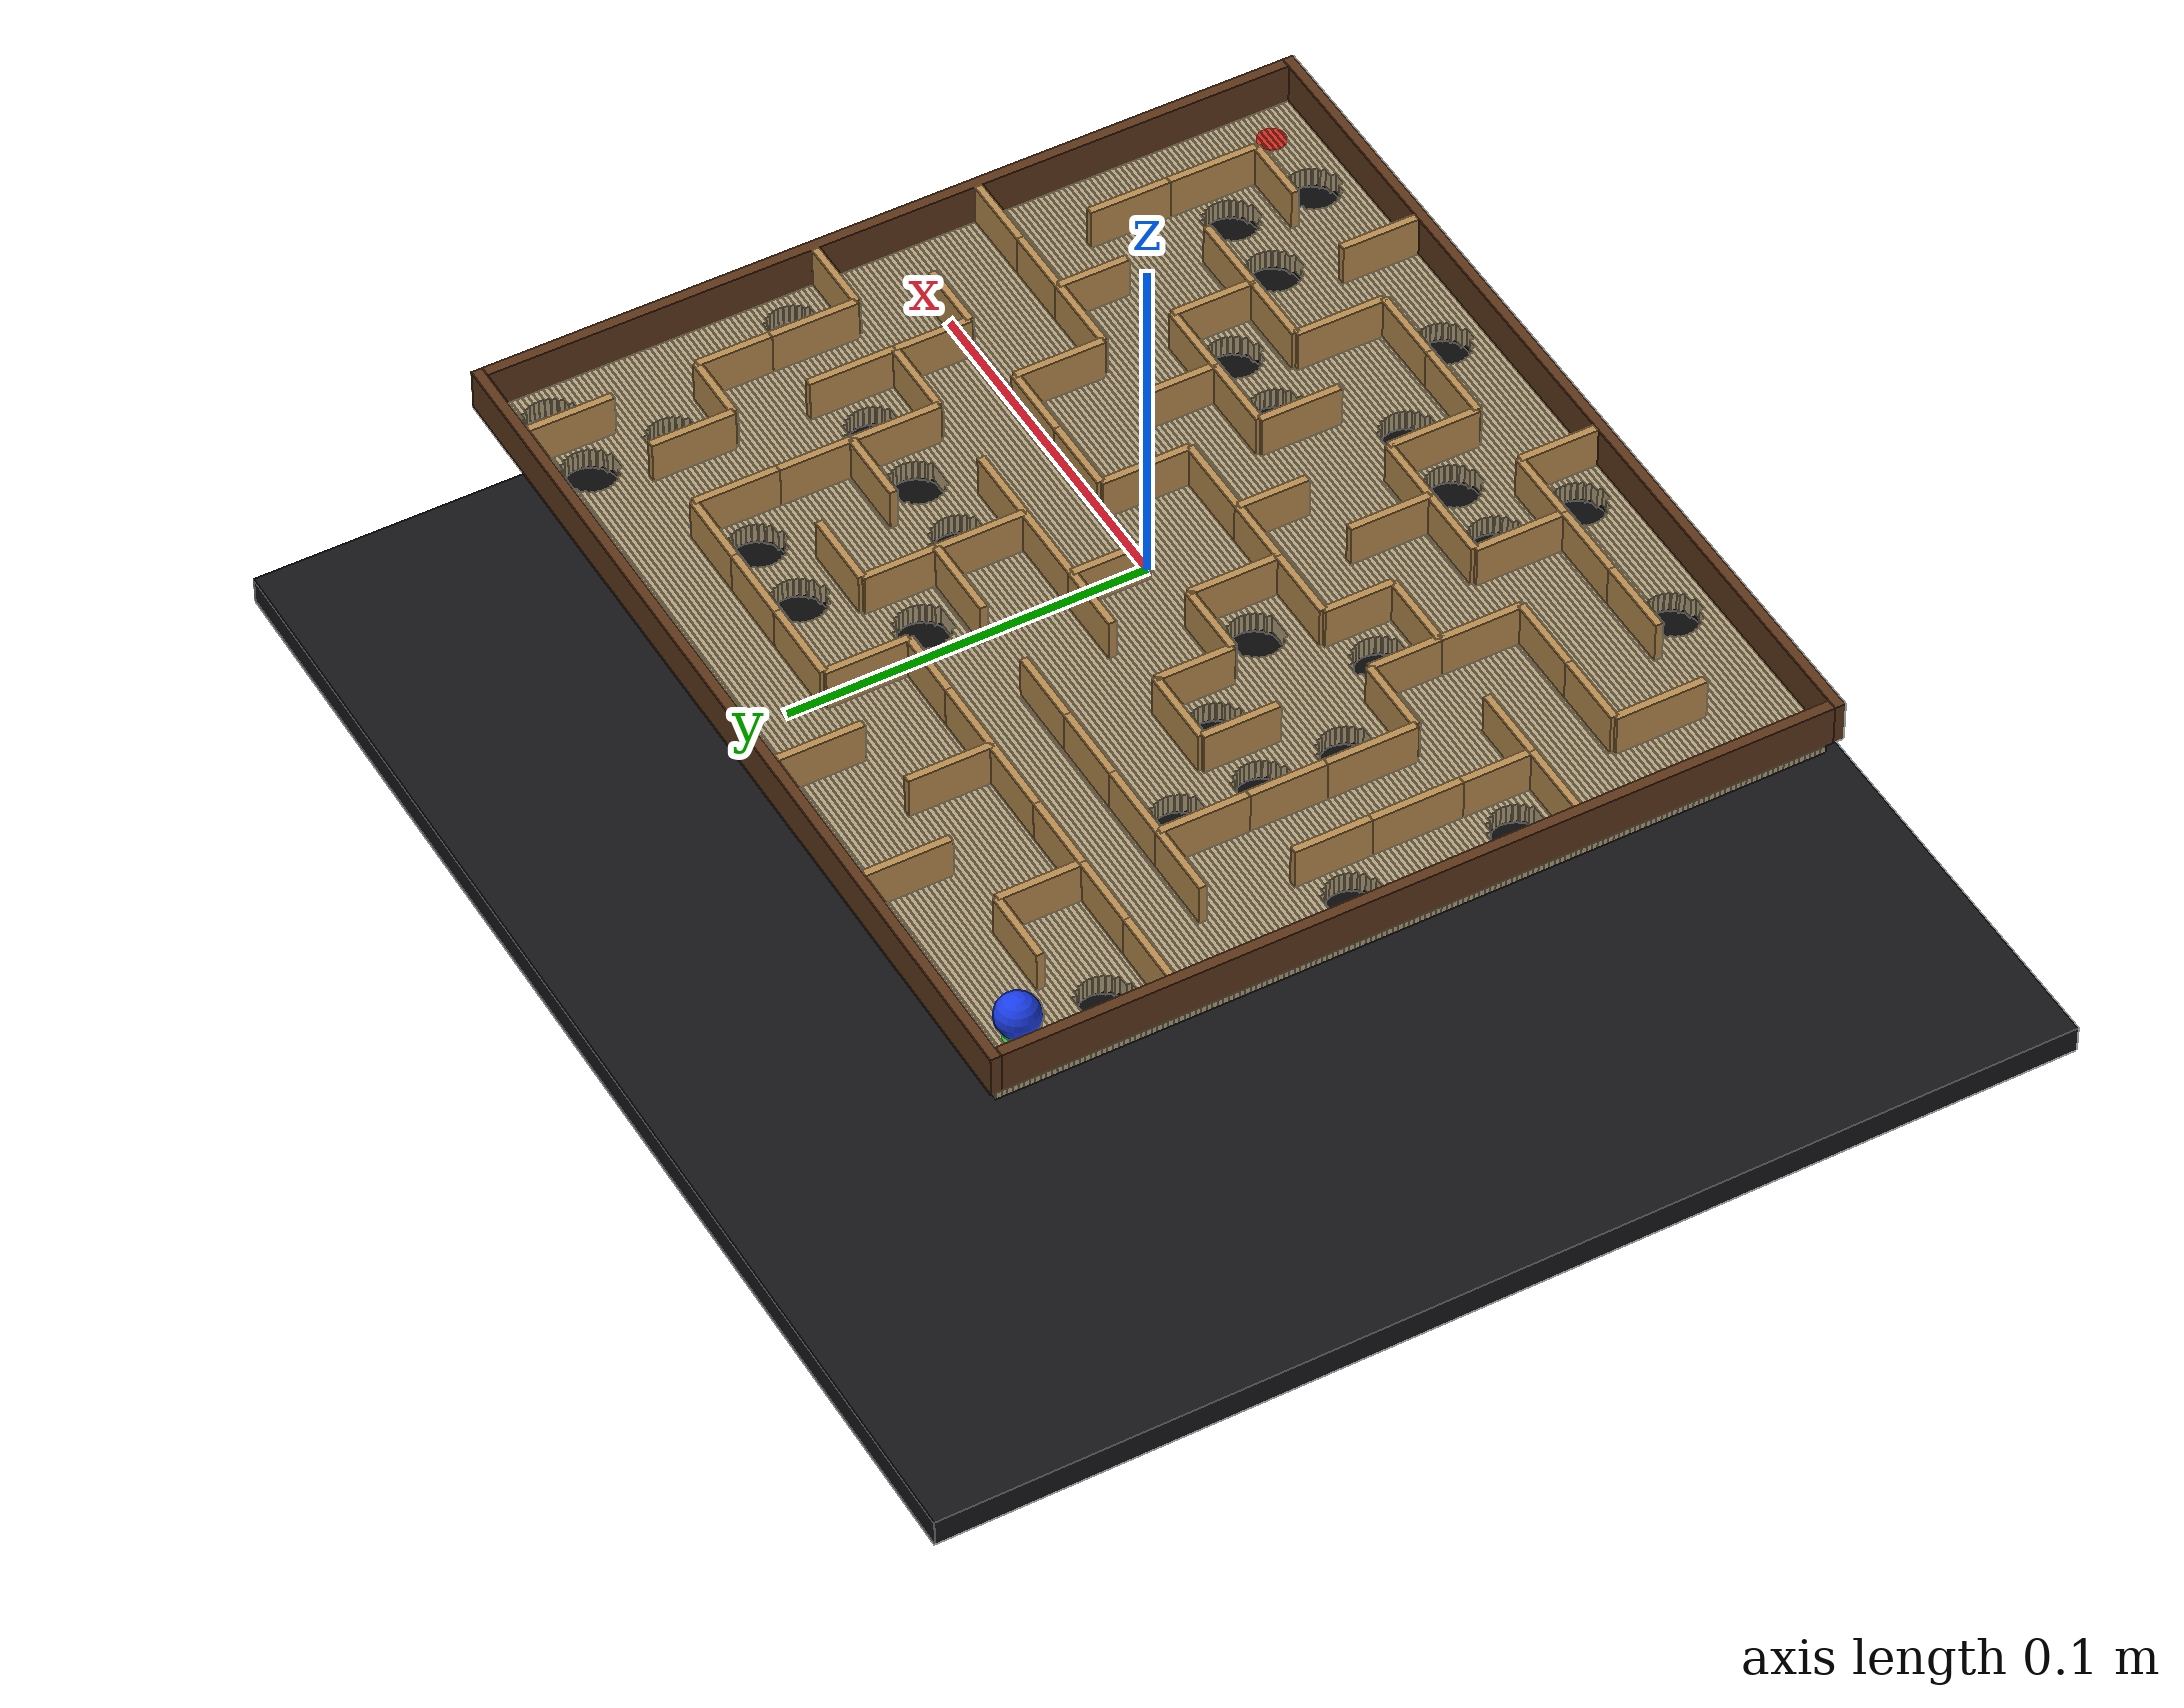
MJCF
<mujoco model="tag_custom_maze">
  <compiler angle="radian" inertiafromgeom="auto"/>
  <option timestep="0.001" gravity="0 0 -9.81" integrator="implicitfast" solver="Newton" iterations="12" tolerance="1e-9"/>
  <size nconmax="4000" njmax="12000"/>
  <visual>
    <global offwidth="900" offheight="800"/>
    <quality shadowsize="2048"/>
    <map znear="0.01" zfar="3"/>
  </visual>
  <default>
    <default class="floor">
      <geom friction="0.3 0.015 0.002" solref="0.004 1" solimp="0.95 0.99 0.001" density="650"/>
    </default>
    <default class="wall">
      <geom friction="0.35 0.02 0.003" solref="0.003 1" solimp="0.95 0.99 0.001" density="700"/>
    </default>
  </default>
  <worldbody>
    <light name="key" pos="0 -0.15 0.55" dir="0 0 -1" diffuse="0.9 0.9 0.9"/>
    <light name="fill" pos="-0.25 0.2 0.35" dir="0.4 -0.3 -1" diffuse="0.45 0.45 0.45"/>
    <camera name="top" pos="0 0 0.43" quat="1 0 0 0" mode="fixed" fovy="37"/>
    <geom name="catch_tray" type="box" pos="0 0 -0.085" size="0.18 0.16 0.004" rgba="0.08 0.08 0.09 1" friction="0.5 0.02 0.003"/>
    <body name="tilt_x_frame" pos="0 0 0">
      <inertial pos="0 0 0" mass="0.02" diaginertia="0.0001 0.0001 0.0001"/>
      <joint name="tilt_x" type="hinge" axis="1 0 0" range="-0.174532925 0.174532925" damping="0.8" armature="0.01"/>
      <body name="board" pos="0 0 0">
        <joint name="tilt_y" type="hinge" axis="0 1 0" range="-0.174532925 0.174532925" damping="0.8" armature="0.01"/>
        <geom name="floor_0" type="box" pos="0 -0.113751634 -0.003" size="0.1295 0.000748366013 0.003" rgba="0.70 0.63 0.48 1" class="floor"/><geom name="floor_1" type="box" pos="0 -0.112254902 -0.003" size="0.1295 0.000748366013 0.003" rgba="0.70 0.63 0.48 1" class="floor"/><geom name="floor_2" type="box" pos="-0.103933962 -0.11075817 -0.003" size="0.0255660376 0.000748366013 0.003" rgba="0.70 0.63 0.48 1" class="floor"/><geom name="floor_3" type="box" pos="-0.0543695918 -0.11075817 -0.003" size="0.0200349454 0.000748366013 0.003" rgba="0.70 0.63 0.48 1" class="floor"/><geom name="floor_4" type="box" pos="0.000316071727 -0.11075817 -0.003" size="0.0306873307 0.000748366013 0.003" rgba="0.70 0.63 0.48 1" class="floor"/><geom name="floor_5" type="box" pos="0.0655136039 -0.11075817 -0.003" size="0.030546814 0.000748366013 0.003" rgba="0.70 0.63 0.48 1" class="floor"/><geom name="floor_6" type="box" pos="0.114761903 -0.11075817 -0.003" size="0.0147380973 0.000748366013 0.003" rgba="0.70 0.63 0.48 1" class="floor"/><geom name="floor_7" type="box" pos="-0.10535869 -0.109261438 -0.003" size="0.0241413103 0.000748366013 0.003" rgba="0.70 0.63 0.48 1" class="floor"/><geom name="floor_8" type="box" pos="-0.0543695918 -0.109261438 -0.003" size="0.0171854907 0.000748366013 0.003" rgba="0.70 0.63 0.48 1" class="floor"/><geom name="floor_9" type="box" pos="0.000316071727 -0.109261438 -0.003" size="0.027837876 0.000748366013 0.003" rgba="0.70 0.63 0.48 1" class="floor"/><geom name="floor_10" type="box" pos="0.0655136039 -0.109261438 -0.003" size="0.0276973594 0.000748366013 0.003" rgba="0.70 0.63 0.48 1" class="floor"/><geom name="floor_11" type="box" pos="0.11618663 -0.109261438 -0.003" size="0.01331337 0.000748366013 0.003" rgba="0.70 0.63 0.48 1" class="floor"/><geom name="floor_12" type="box" pos="-0.106036353 -0.107764706 -0.003" size="0.0234636473 0.000748366013 0.003" rgba="0.70 0.63 0.48 1" class="floor"/><geom name="floor_13" type="box" pos="-0.0543695918 -0.107764706 -0.003" size="0.0158301647 0.000748366013 0.003" rgba="0.70 0.63 0.48 1" class="floor"/><geom name="floor_14" type="box" pos="0.000316071727 -0.107764706 -0.003" size="0.02648255 0.000748366013 0.003" rgba="0.70 0.63 0.48 1" class="floor"/><geom name="floor_15" type="box" pos="0.0655136039 -0.107764706 -0.003" size="0.0263420333 0.000748366013 0.003" rgba="0.70 0.63 0.48 1" class="floor"/><geom name="floor_16" type="box" pos="0.116864293 -0.107764706 -0.003" size="0.0126357069 0.000748366013 0.003" rgba="0.70 0.63 0.48 1" class="floor"/><geom name="floor_17" type="box" pos="-0.106433263 -0.106267974 -0.003" size="0.0230667368 0.000748366013 0.003" rgba="0.70 0.63 0.48 1" class="floor"/><geom name="floor_18" type="box" pos="-0.0543695918 -0.106267974 -0.003" size="0.0150363438 0.000748366013 0.003" rgba="0.70 0.63 0.48 1" class="floor"/><geom name="floor_19" type="box" pos="0.000316071727 -0.106267974 -0.003" size="0.0256887291 0.000748366013 0.003" rgba="0.70 0.63 0.48 1" class="floor"/><geom name="floor_20" type="box" pos="0.0655136039 -0.106267974 -0.003" size="0.0255482124 0.000748366013 0.003" rgba="0.70 0.63 0.48 1" class="floor"/><geom name="floor_21" type="box" pos="0.117261204 -0.106267974 -0.003" size="0.0122387965 0.000748366013 0.003" rgba="0.70 0.63 0.48 1" class="floor"/><geom name="floor_22" type="box" pos="-0.106640958 -0.104771242 -0.003" size="0.0228590416 0.000748366013 0.003" rgba="0.70 0.63 0.48 1" class="floor"/><geom name="floor_23" type="box" pos="-0.0543695918 -0.104771242 -0.003" size="0.0146209534 0.000748366013 0.003" rgba="0.70 0.63 0.48 1" class="floor"/><geom name="floor_24" type="box" pos="0.000316071727 -0.104771242 -0.003" size="0.0252733387 0.000748366013 0.003" rgba="0.70 0.63 0.48 1" class="floor"/><geom name="floor_25" type="box" pos="0.0655136039 -0.104771242 -0.003" size="0.025132822 0.000748366013 0.003" rgba="0.70 0.63 0.48 1" class="floor"/><geom name="floor_26" type="box" pos="0.117468899 -0.104771242 -0.003" size="0.0120311013 0.000748366013 0.003" rgba="0.70 0.63 0.48 1" class="floor"/><geom name="floor_27" type="box" pos="-0.106691028 -0.10327451 -0.003" size="0.0228089718 0.000748366013 0.003" rgba="0.70 0.63 0.48 1" class="floor"/><geom name="floor_28" type="box" pos="-0.0543695918 -0.10327451 -0.003" size="0.0145208138 0.000748366013 0.003" rgba="0.70 0.63 0.48 1" class="floor"/><geom name="floor_29" type="box" pos="0.000316071727 -0.10327451 -0.003" size="0.0251731991 0.000748366013 0.003" rgba="0.70 0.63 0.48 1" class="floor"/><geom name="floor_30" type="box" pos="0.0655136039 -0.10327451 -0.003" size="0.0250326824 0.000748366013 0.003" rgba="0.70 0.63 0.48 1" class="floor"/><geom name="floor_31" type="box" pos="0.117518969 -0.10327451 -0.003" size="0.0119810315 0.000748366013 0.003" rgba="0.70 0.63 0.48 1" class="floor"/><geom name="floor_32" type="box" pos="-0.106589971 -0.101777778 -0.003" size="0.0229100292 0.000748366013 0.003" rgba="0.70 0.63 0.48 1" class="floor"/><geom name="floor_33" type="box" pos="-0.0543695918 -0.101777778 -0.003" size="0.0147229285 0.000748366013 0.003" rgba="0.70 0.63 0.48 1" class="floor"/><geom name="floor_34" type="box" pos="0.000316071727 -0.101777778 -0.003" size="0.0253753138 0.000748366013 0.003" rgba="0.70 0.63 0.48 1" class="floor"/><geom name="floor_35" type="box" pos="0.0655136039 -0.101777778 -0.003" size="0.0252347971 0.000748366013 0.003" rgba="0.70 0.63 0.48 1" class="floor"/><geom name="floor_36" type="box" pos="0.117417911 -0.101777778 -0.003" size="0.0120820888 0.000748366013 0.003" rgba="0.70 0.63 0.48 1" class="floor"/><geom name="floor_37" type="box" pos="-0.106324262 -0.100281046 -0.003" size="0.0231757376 0.000748366013 0.003" rgba="0.70 0.63 0.48 1" class="floor"/><geom name="floor_38" type="box" pos="-0.0543695918 -0.100281046 -0.003" size="0.0152543453 0.000748366013 0.003" rgba="0.70 0.63 0.48 1" class="floor"/><geom name="floor_39" type="box" pos="0.000316071727 -0.100281046 -0.003" size="0.0259067305 0.000748366013 0.003" rgba="0.70 0.63 0.48 1" class="floor"/><geom name="floor_40" type="box" pos="0.0655136039 -0.100281046 -0.003" size="0.0257662139 0.000748366013 0.003" rgba="0.70 0.63 0.48 1" class="floor"/><geom name="floor_41" type="box" pos="0.117152203 -0.100281046 -0.003" size="0.0123477972 0.000748366013 0.003" rgba="0.70 0.63 0.48 1" class="floor"/><geom name="floor_42" type="box" pos="-0.105849084 -0.0987843137 -0.003" size="0.0236509161 0.000748366013 0.003" rgba="0.70 0.63 0.48 1" class="floor"/><geom name="floor_43" type="box" pos="-0.0543695918 -0.0987843137 -0.003" size="0.0162047024 0.000748366013 0.003" rgba="0.70 0.63 0.48 1" class="floor"/><geom name="floor_44" type="box" pos="0.000316071727 -0.0987843137 -0.003" size="0.0268570877 0.000748366013 0.003" rgba="0.70 0.63 0.48 1" class="floor"/><geom name="floor_45" type="box" pos="0.0655136039 -0.0987843137 -0.003" size="0.026716571 0.000748366013 0.003" rgba="0.70 0.63 0.48 1" class="floor"/><geom name="floor_46" type="box" pos="0.116677024 -0.0987843137 -0.003" size="0.0128229758 0.000748366013 0.003" rgba="0.70 0.63 0.48 1" class="floor"/><geom name="floor_47" type="box" pos="-0.105025673 -0.0972875817 -0.003" size="0.0244743269 0.000748366013 0.003" rgba="0.70 0.63 0.48 1" class="floor"/><geom name="floor_48" type="box" pos="-0.0543695918 -0.0972875817 -0.003" size="0.0178515239 0.000748366013 0.003" rgba="0.70 0.63 0.48 1" class="floor"/><geom name="floor_49" type="box" pos="0.000316071727 -0.0972875817 -0.003" size="0.0285039092 0.000748366013 0.003" rgba="0.70 0.63 0.48 1" class="floor"/><geom name="floor_50" type="box" pos="0.0655136039 -0.0972875817 -0.003" size="0.0283633925 0.000748366013 0.003" rgba="0.70 0.63 0.48 1" class="floor"/><geom name="floor_51" type="box" pos="0.115853613 -0.0972875817 -0.003" size="0.0136463865 0.000748366013 0.003" rgba="0.70 0.63 0.48 1" class="floor"/><geom name="floor_52" type="box" pos="0 -0.0957908497 -0.003" size="0.1295 0.000748366013 0.003" rgba="0.70 0.63 0.48 1" class="floor"/><geom name="floor_53" type="box" pos="0 -0.0942941176 -0.003" size="0.1295 0.000748366013 0.003" rgba="0.70 0.63 0.48 1" class="floor"/><geom name="floor_54" type="box" pos="0 -0.0927973856 -0.003" size="0.1295 0.000748366013 0.003" rgba="0.70 0.63 0.48 1" class="floor"/><geom name="floor_55" type="box" pos="0 -0.0913006536 -0.003" size="0.1295 0.000748366013 0.003" rgba="0.70 0.63 0.48 1" class="floor"/><geom name="floor_56" type="box" pos="0 -0.0898039216 -0.003" size="0.1295 0.000748366013 0.003" rgba="0.70 0.63 0.48 1" class="floor"/><geom name="floor_57" type="box" pos="0 -0.0883071895 -0.003" size="0.1295 0.000748366013 0.003" rgba="0.70 0.63 0.48 1" class="floor"/><geom name="floor_58" type="box" pos="-0.0822271653 -0.0868104575 -0.003" size="0.0472728347 0.000748366013 0.003" rgba="0.70 0.63 0.48 1" class="floor"/><geom name="floor_59" type="box" pos="-0.0220153935 -0.0868104575 -0.003" size="0.00773618137 0.000748366013 0.003" rgba="0.70 0.63 0.48 1" class="floor"/><geom name="floor_60" type="box" pos="-0.000761566594 -0.0868104575 -0.003" size="0.00831488984 0.000748366013 0.003" rgba="0.70 0.63 0.48 1" class="floor"/><geom name="floor_61" type="box" pos="0.0434575132 -0.0868104575 -0.003" size="0.0307014343 0.000748366013 0.003" rgba="0.70 0.63 0.48 1" class="floor"/><geom name="floor_62" type="box" pos="0.0874012185 -0.0868104575 -0.003" size="0.00803951529 0.000748366013 0.003" rgba="0.70 0.63 0.48 1" class="floor"/><geom name="floor_63" type="box" pos="0.115071745 -0.0868104575 -0.003" size="0.0144282552 0.000748366013 0.003" rgba="0.70 0.63 0.48 1" class="floor"/><geom name="floor_64" type="box" pos="-0.0834555174 -0.0853137255 -0.003" size="0.0460444826 0.000748366013 0.003" rgba="0.70 0.63 0.48 1" class="floor"/><geom name="floor_65" type="box" pos="-0.0220153935 -0.0853137255 -0.003" size="0.00527947716 0.000748366013 0.003" rgba="0.70 0.63 0.48 1" class="floor"/><geom name="floor_66" type="box" pos="-0.000761566594 -0.0853137255 -0.003" size="0.00585818562 0.000748366013 0.003" rgba="0.70 0.63 0.48 1" class="floor"/><geom name="floor_67" type="box" pos="0.0434575132 -0.0853137255 -0.003" size="0.0282447301 0.000748366013 0.003" rgba="0.70 0.63 0.48 1" class="floor"/><geom name="floor_68" type="box" pos="0.0874012185 -0.0853137255 -0.003" size="0.00558281108 0.000748366013 0.003" rgba="0.70 0.63 0.48 1" class="floor"/><geom name="floor_69" type="box" pos="0.116300097 -0.0853137255 -0.003" size="0.0131999031 0.000748366013 0.003" rgba="0.70 0.63 0.48 1" class="floor"/><geom name="floor_70" type="box" pos="-0.0840856221 -0.0838169935 -0.003" size="0.0454143779 0.000748366013 0.003" rgba="0.70 0.63 0.48 1" class="floor"/><geom name="floor_71" type="box" pos="-0.0220153935 -0.0838169935 -0.003" size="0.00401926768 0.000748366013 0.003" rgba="0.70 0.63 0.48 1" class="floor"/><geom name="floor_72" type="box" pos="-0.000761566594 -0.0838169935 -0.003" size="0.00459797614 0.000748366013 0.003" rgba="0.70 0.63 0.48 1" class="floor"/><geom name="floor_73" type="box" pos="0.0434575132 -0.0838169935 -0.003" size="0.0269845206 0.000748366013 0.003" rgba="0.70 0.63 0.48 1" class="floor"/><geom name="floor_74" type="box" pos="0.0874012185 -0.0838169935 -0.003" size="0.00432260159 0.000748366013 0.003" rgba="0.70 0.63 0.48 1" class="floor"/><geom name="floor_75" type="box" pos="0.116930202 -0.0838169935 -0.003" size="0.0125697984 0.000748366013 0.003" rgba="0.70 0.63 0.48 1" class="floor"/><geom name="floor_76" type="box" pos="-0.0844541175 -0.0823202614 -0.003" size="0.0450458825 0.000748366013 0.003" rgba="0.70 0.63 0.48 1" class="floor"/><geom name="floor_77" type="box" pos="-0.0220153935 -0.0823202614 -0.003" size="0.00328227691 0.000748366013 0.003" rgba="0.70 0.63 0.48 1" class="floor"/><geom name="floor_78" type="box" pos="-0.000761566594 -0.0823202614 -0.003" size="0.00386098538 0.000748366013 0.003" rgba="0.70 0.63 0.48 1" class="floor"/><geom name="floor_79" type="box" pos="0.0434575132 -0.0823202614 -0.003" size="0.0262475299 0.000748366013 0.003" rgba="0.70 0.63 0.48 1" class="floor"/><geom name="floor_80" type="box" pos="0.0874012185 -0.0823202614 -0.003" size="0.00358561083 0.000748366013 0.003" rgba="0.70 0.63 0.48 1" class="floor"/><geom name="floor_81" type="box" pos="0.117298697 -0.0823202614 -0.003" size="0.012201303 0.000748366013 0.003" rgba="0.70 0.63 0.48 1" class="floor"/><geom name="floor_82" type="box" pos="-0.0846397227 -0.0808235294 -0.003" size="0.0448602773 0.000748366013 0.003" rgba="0.70 0.63 0.48 1" class="floor"/><geom name="floor_83" type="box" pos="-0.0220153935 -0.0808235294 -0.003" size="0.00291106642 0.000748366013 0.003" rgba="0.70 0.63 0.48 1" class="floor"/><geom name="floor_84" type="box" pos="-0.000761566594 -0.0808235294 -0.003" size="0.00348977489 0.000748366013 0.003" rgba="0.70 0.63 0.48 1" class="floor"/><geom name="floor_85" type="box" pos="0.0434575132 -0.0808235294 -0.003" size="0.0258763194 0.000748366013 0.003" rgba="0.70 0.63 0.48 1" class="floor"/><geom name="floor_86" type="box" pos="0.0874012185 -0.0808235294 -0.003" size="0.00321440034 0.000748366013 0.003" rgba="0.70 0.63 0.48 1" class="floor"/><geom name="floor_87" type="box" pos="0.117484302 -0.0808235294 -0.003" size="0.0120156978 0.000748366013 0.003" rgba="0.70 0.63 0.48 1" class="floor"/><geom name="floor_88" type="box" pos="-0.0846697426 -0.0793267974 -0.003" size="0.0448302574 0.000748366013 0.003" rgba="0.70 0.63 0.48 1" class="floor"/><geom name="floor_89" type="box" pos="-0.0220153935 -0.0793267974 -0.003" size="0.00285102674 0.000748366013 0.003" rgba="0.70 0.63 0.48 1" class="floor"/><geom name="floor_90" type="box" pos="-0.000761566594 -0.0793267974 -0.003" size="0.0034297352 0.000748366013 0.003" rgba="0.70 0.63 0.48 1" class="floor"/><geom name="floor_91" type="box" pos="0.0434575132 -0.0793267974 -0.003" size="0.0258162797 0.000748366013 0.003" rgba="0.70 0.63 0.48 1" class="floor"/><geom name="floor_92" type="box" pos="0.0874012185 -0.0793267974 -0.003" size="0.00315436065 0.000748366013 0.003" rgba="0.70 0.63 0.48 1" class="floor"/><geom name="floor_93" type="box" pos="0.117514322 -0.0793267974 -0.003" size="0.0119856779 0.000748366013 0.003" rgba="0.70 0.63 0.48 1" class="floor"/><geom name="floor_94" type="box" pos="-0.0845480481 -0.0778300654 -0.003" size="0.0449519519 0.000748366013 0.003" rgba="0.70 0.63 0.48 1" class="floor"/><geom name="floor_95" type="box" pos="-0.0220153935 -0.0778300654 -0.003" size="0.00309441567 0.000748366013 0.003" rgba="0.70 0.63 0.48 1" class="floor"/><geom name="floor_96" type="box" pos="-0.000761566594 -0.0778300654 -0.003" size="0.00367312414 0.000748366013 0.003" rgba="0.70 0.63 0.48 1" class="floor"/><geom name="floor_97" type="box" pos="0.0434575132 -0.0778300654 -0.003" size="0.0260596686 0.000748366013 0.003" rgba="0.70 0.63 0.48 1" class="floor"/><geom name="floor_98" type="box" pos="0.0874012185 -0.0778300654 -0.003" size="0.00339774959 0.000748366013 0.003" rgba="0.70 0.63 0.48 1" class="floor"/><geom name="floor_99" type="box" pos="0.117392628 -0.0778300654 -0.003" size="0.0121073724 0.000748366013 0.003" rgba="0.70 0.63 0.48 1" class="floor"/><geom name="floor_100" type="box" pos="-0.0842580554 -0.0763333333 -0.003" size="0.0452419446 0.000748366013 0.003" rgba="0.70 0.63 0.48 1" class="floor"/><geom name="floor_101" type="box" pos="-0.0220153935 -0.0763333333 -0.003" size="0.0036744012 0.000748366013 0.003" rgba="0.70 0.63 0.48 1" class="floor"/><geom name="floor_102" type="box" pos="-0.000761566594 -0.0763333333 -0.003" size="0.00425310967 0.000748366013 0.003" rgba="0.70 0.63 0.48 1" class="floor"/><geom name="floor_103" type="box" pos="0.0434575132 -0.0763333333 -0.003" size="0.0266396542 0.000748366013 0.003" rgba="0.70 0.63 0.48 1" class="floor"/><geom name="floor_104" type="box" pos="0.0874012185 -0.0763333333 -0.003" size="0.00397773512 0.000748366013 0.003" rgba="0.70 0.63 0.48 1" class="floor"/><geom name="floor_105" type="box" pos="0.117102635 -0.0763333333 -0.003" size="0.0123973652 0.000748366013 0.003" rgba="0.70 0.63 0.48 1" class="floor"/><geom name="floor_106" type="box" pos="-0.0837483466 -0.0748366013 -0.003" size="0.0457516534 0.000748366013 0.003" rgba="0.70 0.63 0.48 1" class="floor"/><geom name="floor_107" type="box" pos="-0.0220153935 -0.0748366013 -0.003" size="0.00469381866 0.000748366013 0.003" rgba="0.70 0.63 0.48 1" class="floor"/><geom name="floor_108" type="box" pos="-0.000761566594 -0.0748366013 -0.003" size="0.00527252712 0.000748366013 0.003" rgba="0.70 0.63 0.48 1" class="floor"/><geom name="floor_109" type="box" pos="0.0434575132 -0.0748366013 -0.003" size="0.0276590716 0.000748366013 0.003" rgba="0.70 0.63 0.48 1" class="floor"/><geom name="floor_110" type="box" pos="0.0874012185 -0.0748366013 -0.003" size="0.00499715257 0.000748366013 0.003" rgba="0.70 0.63 0.48 1" class="floor"/><geom name="floor_111" type="box" pos="0.116592926 -0.0748366013 -0.003" size="0.0129070739 0.000748366013 0.003" rgba="0.70 0.63 0.48 1" class="floor"/><geom name="floor_112" type="box" pos="-0.0828516729 -0.0733398693 -0.003" size="0.0466483271 0.000748366013 0.003" rgba="0.70 0.63 0.48 1" class="floor"/><geom name="floor_113" type="box" pos="-0.0220153935 -0.0733398693 -0.003" size="0.00648716615 0.000748366013 0.003" rgba="0.70 0.63 0.48 1" class="floor"/><geom name="floor_114" type="box" pos="-0.000761566594 -0.0733398693 -0.003" size="0.00706587462 0.000748366013 0.003" rgba="0.70 0.63 0.48 1" class="floor"/><geom name="floor_115" type="box" pos="0.0434575132 -0.0733398693 -0.003" size="0.0294524191 0.000748366013 0.003" rgba="0.70 0.63 0.48 1" class="floor"/><geom name="floor_116" type="box" pos="0.0874012185 -0.0733398693 -0.003" size="0.00679050007 0.000748366013 0.003" rgba="0.70 0.63 0.48 1" class="floor"/><geom name="floor_117" type="box" pos="0.115696252 -0.0733398693 -0.003" size="0.0138037476 0.000748366013 0.003" rgba="0.70 0.63 0.48 1" class="floor"/><geom name="floor_118" type="box" pos="0 -0.0718431373 -0.003" size="0.1295 0.000748366013 0.003" rgba="0.70 0.63 0.48 1" class="floor"/><geom name="floor_119" type="box" pos="0 -0.0703464052 -0.003" size="0.1295 0.000748366013 0.003" rgba="0.70 0.63 0.48 1" class="floor"/><geom name="floor_120" type="box" pos="0 -0.0688496732 -0.003" size="0.1295 0.000748366013 0.003" rgba="0.70 0.63 0.48 1" class="floor"/><geom name="floor_121" type="box" pos="0 -0.0673529412 -0.003" size="0.1295 0.000748366013 0.003" rgba="0.70 0.63 0.48 1" class="floor"/><geom name="floor_122" type="box" pos="0 -0.0658562092 -0.003" size="0.1295 0.000748366013 0.003" rgba="0.70 0.63 0.48 1" class="floor"/><geom name="floor_123" type="box" pos="0 -0.0643594771 -0.003" size="0.1295 0.000748366013 0.003" rgba="0.70 0.63 0.48 1" class="floor"/><geom name="floor_124" type="box" pos="-0.0490144795 -0.0628627451 -0.003" size="0.0804855205 0.000748366013 0.003" rgba="0.70 0.63 0.48 1" class="floor"/><geom name="floor_125" type="box" pos="0.0438040258 -0.0628627451 -0.003" size="0.00930487453 0.000748366013 0.003" rgba="0.70 0.63 0.48 1" class="floor"/><geom name="floor_126" type="box" pos="0.0928185052 -0.0628627451 -0.003" size="0.0366814948 0.000748366013 0.003" rgba="0.70 0.63 0.48 1" class="floor"/><geom name="floor_127" type="box" pos="-0.050604839 -0.0613660131 -0.003" size="0.078895161 0.000748366013 0.003" rgba="0.70 0.63 0.48 1" class="floor"/><geom name="floor_128" type="box" pos="0.0438040258 -0.0613660131 -0.003" size="0.00612415546 0.000748366013 0.003" rgba="0.70 0.63 0.48 1" class="floor"/><geom name="floor_129" type="box" pos="0.0944088648 -0.0613660131 -0.003" size="0.0350911352 0.000748366013 0.003" rgba="0.70 0.63 0.48 1" class="floor"/><geom name="floor_130" type="box" pos="-0.0513115079 -0.059869281 -0.003" size="0.0781884921 0.000748366013 0.003" rgba="0.70 0.63 0.48 1" class="floor"/><geom name="floor_131" type="box" pos="0.0438040258 -0.059869281 -0.003" size="0.0047108176 0.000748366013 0.003" rgba="0.70 0.63 0.48 1" class="floor"/><geom name="floor_132" type="box" pos="0.0951155337 -0.059869281 -0.003" size="0.0343844663 0.000748366013 0.003" rgba="0.70 0.63 0.48 1" class="floor"/><geom name="floor_133" type="box" pos="-0.0517250428 -0.058372549 -0.003" size="0.0777749572 0.000748366013 0.003" rgba="0.70 0.63 0.48 1" class="floor"/><geom name="floor_134" type="box" pos="0.0438040258 -0.058372549 -0.003" size="0.00388374779 0.000748366013 0.003" rgba="0.70 0.63 0.48 1" class="floor"/><geom name="floor_135" type="box" pos="0.0955290686 -0.058372549 -0.003" size="0.0339709314 0.000748366013 0.003" rgba="0.70 0.63 0.48 1" class="floor"/><geom name="floor_136" type="box" pos="-0.0519454069 -0.056875817 -0.003" size="0.0775545931 0.000748366013 0.003" rgba="0.70 0.63 0.48 1" class="floor"/><geom name="floor_137" type="box" pos="0.0438040258 -0.056875817 -0.003" size="0.00344301964 0.000748366013 0.003" rgba="0.70 0.63 0.48 1" class="floor"/><geom name="floor_138" type="box" pos="0.0957494327 -0.056875817 -0.003" size="0.0337505673 0.000748366013 0.003" rgba="0.70 0.63 0.48 1" class="floor"/><geom name="floor_139" type="box" pos="-0.0520068164 -0.055379085 -0.003" size="0.0774931836 0.000748366013 0.003" rgba="0.70 0.63 0.48 1" class="floor"/><geom name="floor_140" type="box" pos="0.0438040258 -0.055379085 -0.003" size="0.00332020069 0.000748366013 0.003" rgba="0.70 0.63 0.48 1" class="floor"/><geom name="floor_141" type="box" pos="0.0958108422 -0.055379085 -0.003" size="0.0336891578 0.000748366013 0.003" rgba="0.70 0.63 0.48 1" class="floor"/><geom name="floor_142" type="box" pos="-0.0519172815 -0.0538823529 -0.003" size="0.0775827185 0.000748366013 0.003" rgba="0.70 0.63 0.48 1" class="floor"/><geom name="floor_143" type="box" pos="0.0438040258 -0.0538823529 -0.003" size="0.00349927051 0.000748366013 0.003" rgba="0.70 0.63 0.48 1" class="floor"/><geom name="floor_144" type="box" pos="0.0957213073 -0.0538823529 -0.003" size="0.0337786927 0.000748366013 0.003" rgba="0.70 0.63 0.48 1" class="floor"/><geom name="floor_145" type="box" pos="-0.0516649242 -0.0523856209 -0.003" size="0.0778350758 0.000748366013 0.003" rgba="0.70 0.63 0.48 1" class="floor"/><geom name="floor_146" type="box" pos="0.0438040258 -0.0523856209 -0.003" size="0.00400398501 0.000748366013 0.003" rgba="0.70 0.63 0.48 1" class="floor"/><geom name="floor_147" type="box" pos="0.09546895 -0.0523856209 -0.003" size="0.03403105 0.000748366013 0.003" rgba="0.70 0.63 0.48 1" class="floor"/><geom name="floor_148" type="box" pos="-0.0512082619 -0.0508888889 -0.003" size="0.0782917381 0.000748366013 0.003" rgba="0.70 0.63 0.48 1" class="floor"/><geom name="floor_149" type="box" pos="0.0438040258 -0.0508888889 -0.003" size="0.00491730976 0.000748366013 0.003" rgba="0.70 0.63 0.48 1" class="floor"/><geom name="floor_150" type="box" pos="0.0950122876 -0.0508888889 -0.003" size="0.0344877124 0.000748366013 0.003" rgba="0.70 0.63 0.48 1" class="floor"/><geom name="floor_151" type="box" pos="-0.0504216117 -0.0493921569 -0.003" size="0.0790783883 0.000748366013 0.003" rgba="0.70 0.63 0.48 1" class="floor"/><geom name="floor_152" type="box" pos="0.0438040258 -0.0493921569 -0.003" size="0.00649061003 0.000748366013 0.003" rgba="0.70 0.63 0.48 1" class="floor"/><geom name="floor_153" type="box" pos="0.0942256375 -0.0493921569 -0.003" size="0.0352743625 0.000748366013 0.003" rgba="0.70 0.63 0.48 1" class="floor"/><geom name="floor_154" type="box" pos="0 -0.0478954248 -0.003" size="0.1295 0.000748366013 0.003" rgba="0.70 0.63 0.48 1" class="floor"/><geom name="floor_155" type="box" pos="0 -0.0463986928 -0.003" size="0.1295 0.000748366013 0.003" rgba="0.70 0.63 0.48 1" class="floor"/><geom name="floor_156" type="box" pos="0 -0.0449019608 -0.003" size="0.1295 0.000748366013 0.003" rgba="0.70 0.63 0.48 1" class="floor"/><geom name="floor_157" type="box" pos="0 -0.0434052288 -0.003" size="0.1295 0.000748366013 0.003" rgba="0.70 0.63 0.48 1" class="floor"/><geom name="floor_158" type="box" pos="0 -0.0419084967 -0.003" size="0.1295 0.000748366013 0.003" rgba="0.70 0.63 0.48 1" class="floor"/><geom name="floor_159" type="box" pos="-0.126391874 -0.0404117647 -0.003" size="0.00310812605 0.000748366013 0.003" rgba="0.70 0.63 0.48 1" class="floor"/><geom name="floor_160" type="box" pos="-0.0866400266 -0.0404117647 -0.003" size="0.0283348887 0.000748366013 0.003" rgba="0.70 0.63 0.48 1" class="floor"/><geom name="floor_161" type="box" pos="0.0397518473 -0.0404117647 -0.003" size="0.0897481527 0.000748366013 0.003" rgba="0.70 0.63 0.48 1" class="floor"/><geom name="floor_162" type="box" pos="-0.127217722 -0.0389150327 -0.003" size="0.00228227779 0.000748366013 0.003" rgba="0.70 0.63 0.48 1" class="floor"/><geom name="floor_163" type="box" pos="-0.0866400266 -0.0389150327 -0.003" size="0.0266831922 0.000748366013 0.003" rgba="0.70 0.63 0.48 1" class="floor"/><geom name="floor_164" type="box" pos="0.0405776956 -0.0389150327 -0.003" size="0.0889223044 0.000748366013 0.003" rgba="0.70 0.63 0.48 1" class="floor"/><geom name="floor_165" type="box" pos="-0.1276941 -0.0374183007 -0.003" size="0.00180589993 0.000748366013 0.003" rgba="0.70 0.63 0.48 1" class="floor"/><geom name="floor_166" type="box" pos="-0.0866400266 -0.0374183007 -0.003" size="0.0257304365 0.000748366013 0.003" rgba="0.70 0.63 0.48 1" class="floor"/><geom name="floor_167" type="box" pos="0.0410540734 -0.0374183007 -0.003" size="0.0884459266 0.000748366013 0.003" rgba="0.70 0.63 0.48 1" class="floor"/><geom name="floor_168" type="box" pos="-0.127960665 -0.0359215686 -0.003" size="0.00153933474 0.000748366013 0.003" rgba="0.70 0.63 0.48 1" class="floor"/><geom name="floor_169" type="box" pos="-0.0866400266 -0.0359215686 -0.003" size="0.0251973061 0.000748366013 0.003" rgba="0.70 0.63 0.48 1" class="floor"/><geom name="floor_170" type="box" pos="0.0413206386 -0.0359215686 -0.003" size="0.0881793614 0.000748366013 0.003" rgba="0.70 0.63 0.48 1" class="floor"/><geom name="floor_171" type="box" pos="-0.128062458 -0.0344248366 -0.003" size="0.00143754222 0.000748366013 0.003" rgba="0.70 0.63 0.48 1" class="floor"/><geom name="floor_172" type="box" pos="-0.0866400266 -0.0344248366 -0.003" size="0.0249937211 0.000748366013 0.003" rgba="0.70 0.63 0.48 1" class="floor"/><geom name="floor_173" type="box" pos="0.0414224312 -0.0344248366 -0.003" size="0.0880775688 0.000748366013 0.003" rgba="0.70 0.63 0.48 1" class="floor"/><geom name="floor_174" type="box" pos="-0.128013108 -0.0329281046 -0.003" size="0.00148689209 0.000748366013 0.003" rgba="0.70 0.63 0.48 1" class="floor"/><geom name="floor_175" type="box" pos="-0.0866400266 -0.0329281046 -0.003" size="0.0250924208 0.000748366013 0.003" rgba="0.70 0.63 0.48 1" class="floor"/><geom name="floor_176" type="box" pos="0.0413730813 -0.0329281046 -0.003" size="0.0881269187 0.000748366013 0.003" rgba="0.70 0.63 0.48 1" class="floor"/><geom name="floor_177" type="box" pos="-0.127806213 -0.0314313725 -0.003" size="0.00169378727 0.000748366013 0.003" rgba="0.70 0.63 0.48 1" class="floor"/><geom name="floor_178" type="box" pos="-0.0866400266 -0.0314313725 -0.003" size="0.0255062112 0.000748366013 0.003" rgba="0.70 0.63 0.48 1" class="floor"/><geom name="floor_179" type="box" pos="0.0411661861 -0.0314313725 -0.003" size="0.0883338139 0.000748366013 0.003" rgba="0.70 0.63 0.48 1" class="floor"/><geom name="floor_180" type="box" pos="-0.127410344 -0.0299346405 -0.003" size="0.00208965617 0.000748366013 0.003" rgba="0.70 0.63 0.48 1" class="floor"/><geom name="floor_181" type="box" pos="-0.0866400266 -0.0299346405 -0.003" size="0.026297949 0.000748366013 0.003" rgba="0.70 0.63 0.48 1" class="floor"/><geom name="floor_182" type="box" pos="0.0407703172 -0.0299346405 -0.003" size="0.0887296828 0.000748366013 0.003" rgba="0.70 0.63 0.48 1" class="floor"/><geom name="floor_183" type="box" pos="-0.126734468 -0.0284379085 -0.003" size="0.00276553222 0.000748366013 0.003" rgba="0.70 0.63 0.48 1" class="floor"/><geom name="floor_184" type="box" pos="-0.0866400266 -0.0284379085 -0.003" size="0.0276497011 0.000748366013 0.003" rgba="0.70 0.63 0.48 1" class="floor"/><geom name="floor_185" type="box" pos="0.0400944412 -0.0284379085 -0.003" size="0.0894055588 0.000748366013 0.003" rgba="0.70 0.63 0.48 1" class="floor"/><geom name="floor_186" type="box" pos="-0.125318437 -0.0269411765 -0.003" size="0.00418156263 0.000748366013 0.003" rgba="0.70 0.63 0.48 1" class="floor"/><geom name="floor_187" type="box" pos="-0.0866400266 -0.0269411765 -0.003" size="0.0304817619 0.000748366013 0.003" rgba="0.70 0.63 0.48 1" class="floor"/><geom name="floor_188" type="box" pos="0.0386784107 -0.0269411765 -0.003" size="0.0908215893 0.000748366013 0.003" rgba="0.70 0.63 0.48 1" class="floor"/><geom name="floor_189" type="box" pos="0 -0.0254444444 -0.003" size="0.1295 0.000748366013 0.003" rgba="0.70 0.63 0.48 1" class="floor"/><geom name="floor_190" type="box" pos="0 -0.0239477124 -0.003" size="0.1295 0.000748366013 0.003" rgba="0.70 0.63 0.48 1" class="floor"/><geom name="floor_191" type="box" pos="0 -0.0224509804 -0.003" size="0.1295 0.000748366013 0.003" rgba="0.70 0.63 0.48 1" class="floor"/><geom name="floor_192" type="box" pos="0 -0.0209542484 -0.003" size="0.1295 0.000748366013 0.003" rgba="0.70 0.63 0.48 1" class="floor"/><geom name="floor_193" type="box" pos="0 -0.0194575163 -0.003" size="0.1295 0.000748366013 0.003" rgba="0.70 0.63 0.48 1" class="floor"/><geom name="floor_194" type="box" pos="-0.105018418 -0.0179607843 -0.003" size="0.024481582 0.000748366013 0.003" rgba="0.70 0.63 0.48 1" class="floor"/><geom name="floor_195" type="box" pos="-0.0543695918 -0.0179607843 -0.003" size="0.0178660341 0.000748366013 0.003" rgba="0.70 0.63 0.48 1" class="floor"/><geom name="floor_196" type="box" pos="0.0506488262 -0.0179607843 -0.003" size="0.0788511738 0.000748366013 0.003" rgba="0.70 0.63 0.48 1" class="floor"/><geom name="floor_197" type="box" pos="-0.105845135 -0.0164640523 -0.003" size="0.0236548646 0.000748366013 0.003" rgba="0.70 0.63 0.48 1" class="floor"/><geom name="floor_198" type="box" pos="-0.0543695918 -0.0164640523 -0.003" size="0.0162125992 0.000748366013 0.003" rgba="0.70 0.63 0.48 1" class="floor"/><geom name="floor_199" type="box" pos="0.0514755436 -0.0164640523 -0.003" size="0.0780244564 0.000748366013 0.003" rgba="0.70 0.63 0.48 1" class="floor"/><geom name="floor_200" type="box" pos="-0.10632194 -0.0149673203 -0.003" size="0.0231780599 0.000748366013 0.003" rgba="0.70 0.63 0.48 1" class="floor"/><geom name="floor_201" type="box" pos="-0.0543695918 -0.0149673203 -0.003" size="0.01525899 0.000748366013 0.003" rgba="0.70 0.63 0.48 1" class="floor"/><geom name="floor_202" type="box" pos="0.0519523482 -0.0149673203 -0.003" size="0.0775476518 0.000748366013 0.003" rgba="0.70 0.63 0.48 1" class="floor"/><geom name="floor_203" type="box" pos="-0.10658881 -0.0134705882 -0.003" size="0.0229111901 0.000748366013 0.003" rgba="0.70 0.63 0.48 1" class="floor"/><geom name="floor_204" type="box" pos="-0.0543695918 -0.0134705882 -0.003" size="0.0147252503 0.000748366013 0.003" rgba="0.70 0.63 0.48 1" class="floor"/><geom name="floor_205" type="box" pos="0.0522192181 -0.0134705882 -0.003" size="0.0772807819 0.000748366013 0.003" rgba="0.70 0.63 0.48 1" class="floor"/><geom name="floor_206" type="box" pos="-0.106690864 -0.0119738562 -0.003" size="0.0228091363 0.000748366013 0.003" rgba="0.70 0.63 0.48 1" class="floor"/><geom name="floor_207" type="box" pos="-0.0543695918 -0.0119738562 -0.003" size="0.0145211426 0.000748366013 0.003" rgba="0.70 0.63 0.48 1" class="floor"/><geom name="floor_208" type="box" pos="0.0523212719 -0.0119738562 -0.003" size="0.0771787281 0.000748366013 0.003" rgba="0.70 0.63 0.48 1" class="floor"/><geom name="floor_209" type="box" pos="-0.10664177 -0.0104771242 -0.003" size="0.0228582303 0.000748366013 0.003" rgba="0.70 0.63 0.48 1" class="floor"/><geom name="floor_210" type="box" pos="-0.0543695918 -0.0104771242 -0.003" size="0.0146193308 0.000748366013 0.003" rgba="0.70 0.63 0.48 1" class="floor"/><geom name="floor_211" type="box" pos="0.0522721778 -0.0104771242 -0.003" size="0.0772278222 0.000748366013 0.003" rgba="0.70 0.63 0.48 1" class="floor"/><geom name="floor_212" type="box" pos="-0.106435159 -0.00898039216 -0.003" size="0.0230648414 0.000748366013 0.003" rgba="0.70 0.63 0.48 1" class="floor"/><geom name="floor_213" type="box" pos="-0.0543695918 -0.00898039216 -0.003" size="0.015032553 0.000748366013 0.003" rgba="0.70 0.63 0.48 1" class="floor"/><geom name="floor_214" type="box" pos="0.0520655667 -0.00898039216 -0.003" size="0.0774344333 0.000748366013 0.003" rgba="0.70 0.63 0.48 1" class="floor"/><geom name="floor_215" type="box" pos="-0.106039659 -0.00748366013 -0.003" size="0.0234603407 0.000748366013 0.003" rgba="0.70 0.63 0.48 1" class="floor"/><geom name="floor_216" type="box" pos="-0.0543695918 -0.00748366013 -0.003" size="0.0158235515 0.000748366013 0.003" rgba="0.70 0.63 0.48 1" class="floor"/><geom name="floor_217" type="box" pos="0.0516700675 -0.00748366013 -0.003" size="0.0778299325 0.000748366013 0.003" rgba="0.70 0.63 0.48 1" class="floor"/><geom name="floor_218" type="box" pos="-0.105364417 -0.0059869281 -0.003" size="0.0241355834 0.000748366013 0.003" rgba="0.70 0.63 0.48 1" class="floor"/><geom name="floor_219" type="box" pos="-0.0543695918 -0.0059869281 -0.003" size="0.0171740368 0.000748366013 0.003" rgba="0.70 0.63 0.48 1" class="floor"/><geom name="floor_220" type="box" pos="0.0509948248 -0.0059869281 -0.003" size="0.0785051752 0.000748366013 0.003" rgba="0.70 0.63 0.48 1" class="floor"/><geom name="floor_221" type="box" pos="-0.103951437 -0.00449019608 -0.003" size="0.0255485634 0.000748366013 0.003" rgba="0.70 0.63 0.48 1" class="floor"/><geom name="floor_222" type="box" pos="-0.0543695918 -0.00449019608 -0.003" size="0.019999997 0.000748366013 0.003" rgba="0.70 0.63 0.48 1" class="floor"/><geom name="floor_223" type="box" pos="0.0495818447 -0.00449019608 -0.003" size="0.0799181553 0.000748366013 0.003" rgba="0.70 0.63 0.48 1" class="floor"/><geom name="floor_224" type="box" pos="0 -0.00299346405 -0.003" size="0.1295 0.000748366013 0.003" rgba="0.70 0.63 0.48 1" class="floor"/><geom name="floor_225" type="box" pos="0 -0.00149673203 -0.003" size="0.1295 0.000748366013 0.003" rgba="0.70 0.63 0.48 1" class="floor"/><geom name="floor_226" type="box" pos="0 -1.38777878e-17 -0.003" size="0.1295 0.000748366013 0.003" rgba="0.70 0.63 0.48 1" class="floor"/><geom name="floor_227" type="box" pos="0 0.00149673203 -0.003" size="0.1295 0.000748366013 0.003" rgba="0.70 0.63 0.48 1" class="floor"/><geom name="floor_228" type="box" pos="0 0.00299346405 -0.003" size="0.1295 0.000748366013 0.003" rgba="0.70 0.63 0.48 1" class="floor"/><geom name="floor_229" type="box" pos="-0.125537966 0.00449019608 -0.003" size="0.00396203388 0.000748366013 0.003" rgba="0.70 0.63 0.48 1" class="floor"/><geom name="floor_230" type="box" pos="-0.0977577813 0.00449019608 -0.003" size="0.0189249497 0.000748366013 0.003" rgba="0.70 0.63 0.48 1" class="floor"/><geom name="floor_231" type="box" pos="-0.0652684763 0.00449019608 -0.003" size="0.00867115406 0.000748366013 0.003" rgba="0.70 0.63 0.48 1" class="floor"/><geom name="floor_232" type="box" pos="0.0388979395 0.00449019608 -0.003" size="0.0906020605 0.000748366013 0.003" rgba="0.70 0.63 0.48 1" class="floor"/><geom name="floor_233" type="box" pos="-0.126813089 0.0059869281 -0.003" size="0.00268691103 0.000748366013 0.003" rgba="0.70 0.63 0.48 1" class="floor"/><geom name="floor_234" type="box" pos="-0.0977577813 0.0059869281 -0.003" size="0.016374704 0.000748366013 0.003" rgba="0.70 0.63 0.48 1" class="floor"/><geom name="floor_235" type="box" pos="-0.0652684763 0.0059869281 -0.003" size="0.00612090836 0.000748366013 0.003" rgba="0.70 0.63 0.48 1" class="floor"/><geom name="floor_236" type="box" pos="0.0401730623 0.0059869281 -0.003" size="0.0893269377 0.000748366013 0.003" rgba="0.70 0.63 0.48 1" class="floor"/><geom name="floor_237" type="box" pos="-0.127455951 0.00748366013 -0.003" size="0.0020440495 0.000748366013 0.003" rgba="0.70 0.63 0.48 1" class="floor"/><geom name="floor_238" type="box" pos="-0.0977577813 0.00748366013 -0.003" size="0.0150889809 0.000748366013 0.003" rgba="0.70 0.63 0.48 1" class="floor"/><geom name="floor_239" type="box" pos="-0.0652684763 0.00748366013 -0.003" size="0.00483518529 0.000748366013 0.003" rgba="0.70 0.63 0.48 1" class="floor"/><geom name="floor_240" type="box" pos="0.0408159239 0.00748366013 -0.003" size="0.0886840761 0.000748366013 0.003" rgba="0.70 0.63 0.48 1" class="floor"/><geom name="floor_241" type="box" pos="-0.12783221 0.00898039216 -0.003" size="0.00166778996 0.000748366013 0.003" rgba="0.70 0.63 0.48 1" class="floor"/><geom name="floor_242" type="box" pos="-0.0977577813 0.00898039216 -0.003" size="0.0143364619 0.000748366013 0.003" rgba="0.70 0.63 0.48 1" class="floor"/><geom name="floor_243" type="box" pos="-0.0652684763 0.00898039216 -0.003" size="0.00408266622 0.000748366013 0.003" rgba="0.70 0.63 0.48 1" class="floor"/><geom name="floor_244" type="box" pos="0.0411921834 0.00898039216 -0.003" size="0.0883078166 0.000748366013 0.003" rgba="0.70 0.63 0.48 1" class="floor"/><geom name="floor_245" type="box" pos="-0.128023906 0.0104771242 -0.003" size="0.00147609412 0.000748366013 0.003" rgba="0.70 0.63 0.48 1" class="floor"/><geom name="floor_246" type="box" pos="-0.0977577813 0.0104771242 -0.003" size="0.0139530702 0.000748366013 0.003" rgba="0.70 0.63 0.48 1" class="floor"/><geom name="floor_247" type="box" pos="-0.0652684763 0.0104771242 -0.003" size="0.00369927453 0.000748366013 0.003" rgba="0.70 0.63 0.48 1" class="floor"/><geom name="floor_248" type="box" pos="0.0413838793 0.0104771242 -0.003" size="0.0881161207 0.000748366013 0.003" rgba="0.70 0.63 0.48 1" class="floor"/><geom name="floor_249" type="box" pos="-0.128059489 0.0119738562 -0.003" size="0.00144051069 0.000748366013 0.003" rgba="0.70 0.63 0.48 1" class="floor"/><geom name="floor_250" type="box" pos="-0.0977577813 0.0119738562 -0.003" size="0.0138819033 0.000748366013 0.003" rgba="0.70 0.63 0.48 1" class="floor"/><geom name="floor_251" type="box" pos="-0.0652684763 0.0119738562 -0.003" size="0.00362810768 0.000748366013 0.003" rgba="0.70 0.63 0.48 1" class="floor"/><geom name="floor_252" type="box" pos="0.0414194627 0.0119738562 -0.003" size="0.0880805373 0.000748366013 0.003" rgba="0.70 0.63 0.48 1" class="floor"/><geom name="floor_253" type="box" pos="-0.127943556 0.0134705882 -0.003" size="0.00155644445 0.000748366013 0.003" rgba="0.70 0.63 0.48 1" class="floor"/><geom name="floor_254" type="box" pos="-0.0977577813 0.0134705882 -0.003" size="0.0141137708 0.000748366013 0.003" rgba="0.70 0.63 0.48 1" class="floor"/><geom name="floor_255" type="box" pos="-0.0652684763 0.0134705882 -0.003" size="0.00385997519 0.000748366013 0.003" rgba="0.70 0.63 0.48 1" class="floor"/><geom name="floor_256" type="box" pos="0.0413035289 0.0134705882 -0.003" size="0.0881964711 0.000748366013 0.003" rgba="0.70 0.63 0.48 1" class="floor"/><geom name="floor_257" type="box" pos="-0.127660391 0.0149673203 -0.003" size="0.00183960929 0.000748366013 0.003" rgba="0.70 0.63 0.48 1" class="floor"/><geom name="floor_258" type="box" pos="-0.0977577813 0.0149673203 -0.003" size="0.0146801005 0.000748366013 0.003" rgba="0.70 0.63 0.48 1" class="floor"/><geom name="floor_259" type="box" pos="-0.0652684763 0.0149673203 -0.003" size="0.00442630487 0.000748366013 0.003" rgba="0.70 0.63 0.48 1" class="floor"/><geom name="floor_260" type="box" pos="0.0410203641 0.0149673203 -0.003" size="0.0884796359 0.000748366013 0.003" rgba="0.70 0.63 0.48 1" class="floor"/><geom name="floor_261" type="box" pos="-0.127160506 0.0164640523 -0.003" size="0.00233949405 0.000748366013 0.003" rgba="0.70 0.63 0.48 1" class="floor"/><geom name="floor_262" type="box" pos="-0.0977577813 0.0164640523 -0.003" size="0.01567987 0.000748366013 0.003" rgba="0.70 0.63 0.48 1" class="floor"/><geom name="floor_263" type="box" pos="-0.0652684763 0.0164640523 -0.003" size="0.0054260744 0.000748366013 0.003" rgba="0.70 0.63 0.48 1" class="floor"/><geom name="floor_264" type="box" pos="0.0405204793 0.0164640523 -0.003" size="0.0889795207 0.000748366013 0.003" rgba="0.70 0.63 0.48 1" class="floor"/><geom name="floor_265" type="box" pos="-0.12628536 0.0179607843 -0.003" size="0.00321464048 0.000748366013 0.003" rgba="0.70 0.63 0.48 1" class="floor"/><geom name="floor_266" type="box" pos="-0.0977577813 0.0179607843 -0.003" size="0.0174301629 0.000748366013 0.003" rgba="0.70 0.63 0.48 1" class="floor"/><geom name="floor_267" type="box" pos="-0.0652684763 0.0179607843 -0.003" size="0.00717636726 0.000748366013 0.003" rgba="0.70 0.63 0.48 1" class="floor"/><geom name="floor_268" type="box" pos="0.0396453329 0.0179607843 -0.003" size="0.0898546671 0.000748366013 0.003" rgba="0.70 0.63 0.48 1" class="floor"/><geom name="floor_269" type="box" pos="0 0.0194575163 -0.003" size="0.1295 0.000748366013 0.003" rgba="0.70 0.63 0.48 1" class="floor"/><geom name="floor_270" type="box" pos="0 0.0209542484 -0.003" size="0.1295 0.000748366013 0.003" rgba="0.70 0.63 0.48 1" class="floor"/><geom name="floor_271" type="box" pos="0 0.0224509804 -0.003" size="0.1295 0.000748366013 0.003" rgba="0.70 0.63 0.48 1" class="floor"/><geom name="floor_272" type="box" pos="0 0.0239477124 -0.003" size="0.1295 0.000748366013 0.003" rgba="0.70 0.63 0.48 1" class="floor"/><geom name="floor_273" type="box" pos="0 0.0254444444 -0.003" size="0.1295 0.000748366013 0.003" rgba="0.70 0.63 0.48 1" class="floor"/><geom name="floor_274" type="box" pos="0 0.0269411765 -0.003" size="0.1295 0.000748366013 0.003" rgba="0.70 0.63 0.48 1" class="floor"/><geom name="floor_275" type="box" pos="-0.105125258 0.0284379085 -0.003" size="0.0243747423 0.000748366013 0.003" rgba="0.70 0.63 0.48 1" class="floor"/><geom name="floor_276" type="box" pos="-0.0217005674 0.0284379085 -0.003" size="0.0503213792 0.000748366013 0.003" rgba="0.70 0.63 0.48 1" class="floor"/><geom name="floor_277" type="box" pos="0.0438040258 0.0284379085 -0.003" size="0.0064546453 0.000748366013 0.003" rgba="0.70 0.63 0.48 1" class="floor"/><geom name="floor_278" type="box" pos="0.0656916404 0.0284379085 -0.003" size="0.00670440068 0.000748366013 0.003" rgba="0.70 0.63 0.48 1" class="floor"/><geom name="floor_279" type="box" pos="0.0977192529 0.0284379085 -0.003" size="0.0165946431 0.000748366013 0.003" rgba="0.70 0.63 0.48 1" class="floor"/><geom name="floor_280" type="box" pos="0.126271232 0.0284379085 -0.003" size="0.00322876767 0.000748366013 0.003" rgba="0.70 0.63 0.48 1" class="floor"/><geom name="floor_281" type="box" pos="-0.105903909 0.0299346405 -0.003" size="0.0235960911 0.000748366013 0.003" rgba="0.70 0.63 0.48 1" class="floor"/><geom name="floor_282" type="box" pos="-0.0217005674 0.0299346405 -0.003" size="0.0487640768 0.000748366013 0.003" rgba="0.70 0.63 0.48 1" class="floor"/><geom name="floor_283" type="box" pos="0.0438040258 0.0299346405 -0.003" size="0.00489734289 0.000748366013 0.003" rgba="0.70 0.63 0.48 1" class="floor"/><geom name="floor_284" type="box" pos="0.0656916404 0.0299346405 -0.003" size="0.00514709827 0.000748366013 0.003" rgba="0.70 0.63 0.48 1" class="floor"/><geom name="floor_285" type="box" pos="0.0977192529 0.0299346405 -0.003" size="0.0150373407 0.000748366013 0.003" rgba="0.70 0.63 0.48 1" class="floor"/><geom name="floor_286" type="box" pos="0.127049884 0.0299346405 -0.003" size="0.00245011646 0.000748366013 0.003" rgba="0.70 0.63 0.48 1" class="floor"/><geom name="floor_287" type="box" pos="-0.106356435 0.0314313725 -0.003" size="0.0231435655 0.000748366013 0.003" rgba="0.70 0.63 0.48 1" class="floor"/><geom name="floor_288" type="box" pos="-0.0217005674 0.0314313725 -0.003" size="0.0478590255 0.000748366013 0.003" rgba="0.70 0.63 0.48 1" class="floor"/><geom name="floor_289" type="box" pos="0.0438040258 0.0314313725 -0.003" size="0.00399229152 0.000748366013 0.003" rgba="0.70 0.63 0.48 1" class="floor"/><geom name="floor_290" type="box" pos="0.0656916404 0.0314313725 -0.003" size="0.0042420469 0.000748366013 0.003" rgba="0.70 0.63 0.48 1" class="floor"/><geom name="floor_291" type="box" pos="0.0977192529 0.0314313725 -0.003" size="0.0141322894 0.000748366013 0.003" rgba="0.70 0.63 0.48 1" class="floor"/><geom name="floor_292" type="box" pos="0.127502409 0.0314313725 -0.003" size="0.00199759078 0.000748366013 0.003" rgba="0.70 0.63 0.48 1" class="floor"/><geom name="floor_293" type="box" pos="-0.106605778 0.0329281046 -0.003" size="0.0228942225 0.000748366013 0.003" rgba="0.70 0.63 0.48 1" class="floor"/><geom name="floor_294" type="box" pos="-0.0217005674 0.0329281046 -0.003" size="0.0473603395 0.000748366013 0.003" rgba="0.70 0.63 0.48 1" class="floor"/><geom name="floor_295" type="box" pos="0.0438040258 0.0329281046 -0.003" size="0.00349360557 0.000748366013 0.003" rgba="0.70 0.63 0.48 1" class="floor"/><geom name="floor_296" type="box" pos="0.0656916404 0.0329281046 -0.003" size="0.00374336095 0.000748366013 0.003" rgba="0.70 0.63 0.48 1" class="floor"/><geom name="floor_297" type="box" pos="0.0977192529 0.0329281046 -0.003" size="0.0136336034 0.000748366013 0.003" rgba="0.70 0.63 0.48 1" class="floor"/><geom name="floor_298" type="box" pos="0.127751752 0.0329281046 -0.003" size="0.0017482478 0.000748366013 0.003" rgba="0.70 0.63 0.48 1" class="floor"/><geom name="floor_299" type="box" pos="-0.106692694 0.0344248366 -0.003" size="0.0228073064 0.000748366013 0.003" rgba="0.70 0.63 0.48 1" class="floor"/><geom name="floor_300" type="box" pos="-0.0217005674 0.0344248366 -0.003" size="0.0471865074 0.000748366013 0.003" rgba="0.70 0.63 0.48 1" class="floor"/><geom name="floor_301" type="box" pos="0.0438040258 0.0344248366 -0.003" size="0.00331977342 0.000748366013 0.003" rgba="0.70 0.63 0.48 1" class="floor"/><geom name="floor_302" type="box" pos="0.0656916404 0.0344248366 -0.003" size="0.0035695288 0.000748366013 0.003" rgba="0.70 0.63 0.48 1" class="floor"/><geom name="floor_303" type="box" pos="0.0977192529 0.0344248366 -0.003" size="0.0134597713 0.000748366013 0.003" rgba="0.70 0.63 0.48 1" class="floor"/><geom name="floor_304" type="box" pos="0.127838668 0.0344248366 -0.003" size="0.00166133173 0.000748366013 0.003" rgba="0.70 0.63 0.48 1" class="floor"/><geom name="floor_305" type="box" pos="-0.106628692 0.0359215686 -0.003" size="0.0228713078 0.000748366013 0.003" rgba="0.70 0.63 0.48 1" class="floor"/><geom name="floor_306" type="box" pos="-0.0217005674 0.0359215686 -0.003" size="0.0473145102 0.000748366013 0.003" rgba="0.70 0.63 0.48 1" class="floor"/><geom name="floor_307" type="box" pos="0.0438040258 0.0359215686 -0.003" size="0.00344777629 0.000748366013 0.003" rgba="0.70 0.63 0.48 1" class="floor"/><geom name="floor_308" type="box" pos="0.0656916404 0.0359215686 -0.003" size="0.00369753167 0.000748366013 0.003" rgba="0.70 0.63 0.48 1" class="floor"/><geom name="floor_309" type="box" pos="0.0977192529 0.0359215686 -0.003" size="0.0135877741 0.000748366013 0.003" rgba="0.70 0.63 0.48 1" class="floor"/><geom name="floor_310" type="box" pos="0.127774667 0.0359215686 -0.003" size="0.00172533316 0.000748366013 0.003" rgba="0.70 0.63 0.48 1" class="floor"/><geom name="floor_311" type="box" pos="-0.106405414 0.0374183007 -0.003" size="0.0230945859 0.000748366013 0.003" rgba="0.70 0.63 0.48 1" class="floor"/><geom name="floor_312" type="box" pos="-0.0217005674 0.0374183007 -0.003" size="0.0477610664 0.000748366013 0.003" rgba="0.70 0.63 0.48 1" class="floor"/><geom name="floor_313" type="box" pos="0.0438040258 0.0374183007 -0.003" size="0.00389433247 0.000748366013 0.003" rgba="0.70 0.63 0.48 1" class="floor"/><geom name="floor_314" type="box" pos="0.0656916404 0.0374183007 -0.003" size="0.00414408785 0.000748366013 0.003" rgba="0.70 0.63 0.48 1" class="floor"/><geom name="floor_315" type="box" pos="0.0977192529 0.0374183007 -0.003" size="0.0140343303 0.000748366013 0.003" rgba="0.70 0.63 0.48 1" class="floor"/><geom name="floor_316" type="box" pos="0.127551389 0.0374183007 -0.003" size="0.00194861125 0.000748366013 0.003" rgba="0.70 0.63 0.48 1" class="floor"/><geom name="floor_317" type="box" pos="-0.10598802 0.0389150327 -0.003" size="0.0235119799 0.000748366013 0.003" rgba="0.70 0.63 0.48 1" class="floor"/><geom name="floor_318" type="box" pos="-0.0217005674 0.0389150327 -0.003" size="0.0485958543 0.000748366013 0.003" rgba="0.70 0.63 0.48 1" class="floor"/><geom name="floor_319" type="box" pos="0.0438040258 0.0389150327 -0.003" size="0.0047291204 0.000748366013 0.003" rgba="0.70 0.63 0.48 1" class="floor"/><geom name="floor_320" type="box" pos="0.0656916404 0.0389150327 -0.003" size="0.00497887578 0.000748366013 0.003" rgba="0.70 0.63 0.48 1" class="floor"/><geom name="floor_321" type="box" pos="0.0977192529 0.0389150327 -0.003" size="0.0148691182 0.000748366013 0.003" rgba="0.70 0.63 0.48 1" class="floor"/><geom name="floor_322" type="box" pos="0.127133995 0.0389150327 -0.003" size="0.00236600522 0.000748366013 0.003" rgba="0.70 0.63 0.48 1" class="floor"/><geom name="floor_323" type="box" pos="-0.105274483 0.0404117647 -0.003" size="0.0242255172 0.000748366013 0.003" rgba="0.70 0.63 0.48 1" class="floor"/><geom name="floor_324" type="box" pos="-0.0217005674 0.0404117647 -0.003" size="0.050022929 0.000748366013 0.003" rgba="0.70 0.63 0.48 1" class="floor"/><geom name="floor_325" type="box" pos="0.0438040258 0.0404117647 -0.003" size="0.00615619506 0.000748366013 0.003" rgba="0.70 0.63 0.48 1" class="floor"/><geom name="floor_326" type="box" pos="0.0656916404 0.0404117647 -0.003" size="0.00640595044 0.000748366013 0.003" rgba="0.70 0.63 0.48 1" class="floor"/><geom name="floor_327" type="box" pos="0.0977192529 0.0404117647 -0.003" size="0.0162961929 0.000748366013 0.003" rgba="0.70 0.63 0.48 1" class="floor"/><geom name="floor_328" type="box" pos="0.126420457 0.0404117647 -0.003" size="0.00307954255 0.000748366013 0.003" rgba="0.70 0.63 0.48 1" class="floor"/><geom name="floor_329" type="box" pos="-0.103635213 0.0419084967 -0.003" size="0.0258647867 0.000748366013 0.003" rgba="0.70 0.63 0.48 1" class="floor"/><geom name="floor_330" type="box" pos="-0.0217005674 0.0419084967 -0.003" size="0.053301468 0.000748366013 0.003" rgba="0.70 0.63 0.48 1" class="floor"/><geom name="floor_331" type="box" pos="0.0438040258 0.0419084967 -0.003" size="0.0094347341 0.000748366013 0.003" rgba="0.70 0.63 0.48 1" class="floor"/><geom name="floor_332" type="box" pos="0.0656916404 0.0419084967 -0.003" size="0.00968448948 0.000748366013 0.003" rgba="0.70 0.63 0.48 1" class="floor"/><geom name="floor_333" type="box" pos="0.0977192529 0.0419084967 -0.003" size="0.0195747319 0.000748366013 0.003" rgba="0.70 0.63 0.48 1" class="floor"/><geom name="floor_334" type="box" pos="0.124781188 0.0419084967 -0.003" size="0.00471881207 0.000748366013 0.003" rgba="0.70 0.63 0.48 1" class="floor"/><geom name="floor_335" type="box" pos="0 0.0434052288 -0.003" size="0.1295 0.000748366013 0.003" rgba="0.70 0.63 0.48 1" class="floor"/><geom name="floor_336" type="box" pos="0 0.0449019608 -0.003" size="0.1295 0.000748366013 0.003" rgba="0.70 0.63 0.48 1" class="floor"/><geom name="floor_337" type="box" pos="0 0.0463986928 -0.003" size="0.1295 0.000748366013 0.003" rgba="0.70 0.63 0.48 1" class="floor"/><geom name="floor_338" type="box" pos="0 0.0478954248 -0.003" size="0.1295 0.000748366013 0.003" rgba="0.70 0.63 0.48 1" class="floor"/><geom name="floor_339" type="box" pos="0 0.0493921569 -0.003" size="0.1295 0.000748366013 0.003" rgba="0.70 0.63 0.48 1" class="floor"/><geom name="floor_340" type="box" pos="-0.0617523296 0.0508888889 -0.003" size="0.0677476704 0.000748366013 0.003" rgba="0.70 0.63 0.48 1" class="floor"/><geom name="floor_341" type="box" pos="0.0719070307 0.0508888889 -0.003" size="0.0575929693 0.000748366013 0.003" rgba="0.70 0.63 0.48 1" class="floor"/><geom name="floor_342" type="box" pos="-0.062577051 0.0523856209 -0.003" size="0.066922949 0.000748366013 0.003" rgba="0.70 0.63 0.48 1" class="floor"/><geom name="floor_343" type="box" pos="0.0727317521 0.0523856209 -0.003" size="0.0567682479 0.000748366013 0.003" rgba="0.70 0.63 0.48 1" class="floor"/><geom name="floor_344" type="box" pos="-0.0630528749 0.0538823529 -0.003" size="0.0664471251 0.000748366013 0.003" rgba="0.70 0.63 0.48 1" class="floor"/><geom name="floor_345" type="box" pos="0.073207576 0.0538823529 -0.003" size="0.056292424 0.000748366013 0.003" rgba="0.70 0.63 0.48 1" class="floor"/><geom name="floor_346" type="box" pos="-0.0633190445 0.055379085 -0.003" size="0.0661809555 0.000748366013 0.003" rgba="0.70 0.63 0.48 1" class="floor"/><geom name="floor_347" type="box" pos="0.0734737456 0.055379085 -0.003" size="0.0560262544 0.000748366013 0.003" rgba="0.70 0.63 0.48 1" class="floor"/><geom name="floor_348" type="box" pos="-0.0634204976 0.056875817 -0.003" size="0.0660795024 0.000748366013 0.003" rgba="0.70 0.63 0.48 1" class="floor"/><geom name="floor_349" type="box" pos="0.0735751987 0.056875817 -0.003" size="0.0559248013 0.000748366013 0.003" rgba="0.70 0.63 0.48 1" class="floor"/><geom name="floor_350" type="box" pos="-0.0633708154 0.058372549 -0.003" size="0.0661291846 0.000748366013 0.003" rgba="0.70 0.63 0.48 1" class="floor"/><geom name="floor_351" type="box" pos="0.0735255164 0.058372549 -0.003" size="0.0559744836 0.000748366013 0.003" rgba="0.70 0.63 0.48 1" class="floor"/><geom name="floor_352" type="box" pos="-0.063163551 0.059869281 -0.003" size="0.066336449 0.000748366013 0.003" rgba="0.70 0.63 0.48 1" class="floor"/><geom name="floor_353" type="box" pos="0.073318252 0.059869281 -0.003" size="0.056181748 0.000748366013 0.003" rgba="0.70 0.63 0.48 1" class="floor"/><geom name="floor_354" type="box" pos="-0.0627672015 0.0613660131 -0.003" size="0.0667327985 0.000748366013 0.003" rgba="0.70 0.63 0.48 1" class="floor"/><geom name="floor_355" type="box" pos="0.0729219025 0.0613660131 -0.003" size="0.0565780975 0.000748366013 0.003" rgba="0.70 0.63 0.48 1" class="floor"/><geom name="floor_356" type="box" pos="-0.0620905013 0.0628627451 -0.003" size="0.0674094987 0.000748366013 0.003" rgba="0.70 0.63 0.48 1" class="floor"/><geom name="floor_357" type="box" pos="0.0722452024 0.0628627451 -0.003" size="0.0572547976 0.000748366013 0.003" rgba="0.70 0.63 0.48 1" class="floor"/><geom name="floor_358" type="box" pos="-0.0606704769 0.0643594771 -0.003" size="0.0688295231 0.000748366013 0.003" rgba="0.70 0.63 0.48 1" class="floor"/><geom name="floor_359" type="box" pos="0.0708251779 0.0643594771 -0.003" size="0.0586748221 0.000748366013 0.003" rgba="0.70 0.63 0.48 1" class="floor"/><geom name="floor_360" type="box" pos="0 0.0658562092 -0.003" size="0.1295 0.000748366013 0.003" rgba="0.70 0.63 0.48 1" class="floor"/><geom name="floor_361" type="box" pos="0 0.0673529412 -0.003" size="0.1295 0.000748366013 0.003" rgba="0.70 0.63 0.48 1" class="floor"/><geom name="floor_362" type="box" pos="0 0.0688496732 -0.003" size="0.1295 0.000748366013 0.003" rgba="0.70 0.63 0.48 1" class="floor"/><geom name="floor_363" type="box" pos="0 0.0703464052 -0.003" size="0.1295 0.000748366013 0.003" rgba="0.70 0.63 0.48 1" class="floor"/><geom name="floor_364" type="box" pos="-0.125096073 0.0718431373 -0.003" size="0.0044039267 0.000748366013 0.003" rgba="0.70 0.63 0.48 1" class="floor"/><geom name="floor_365" type="box" pos="-0.0430721177 0.0718431373 -0.003" size="0.0744943989 0.000748366013 0.003" rgba="0.70 0.63 0.48 1" class="floor"/><geom name="floor_366" type="box" pos="0.0438040258 0.0718431373 -0.003" size="0.00925611464 0.000748366013 0.003" rgba="0.70 0.63 0.48 1" class="floor"/><geom name="floor_367" type="box" pos="0.0763325335 0.0718431373 -0.003" size="0.0201467631 0.000748366013 0.003" rgba="0.70 0.63 0.48 1" class="floor"/><geom name="floor_368" type="box" pos="0.114552463 0.0718431373 -0.003" size="0.0149475367 0.000748366013 0.003" rgba="0.70 0.63 0.48 1" class="floor"/><geom name="floor_369" type="box" pos="-0.126668404 0.0733398693 -0.003" size="0.0028315956 0.000748366013 0.003" rgba="0.70 0.63 0.48 1" class="floor"/><geom name="floor_370" type="box" pos="-0.0430721177 0.0733398693 -0.003" size="0.0713497367 0.000748366013 0.003" rgba="0.70 0.63 0.48 1" class="floor"/><geom name="floor_371" type="box" pos="0.0438040258 0.0733398693 -0.003" size="0.00611145244 0.000748366013 0.003" rgba="0.70 0.63 0.48 1" class="floor"/><geom name="floor_372" type="box" pos="0.0763325335 0.0733398693 -0.003" size="0.017002101 0.000748366013 0.003" rgba="0.70 0.63 0.48 1" class="floor"/><geom name="floor_373" type="box" pos="0.116124794 0.0733398693 -0.003" size="0.0133752056 0.000748366013 0.003" rgba="0.70 0.63 0.48 1" class="floor"/><geom name="floor_374" type="box" pos="-0.127372356 0.0748366013 -0.003" size="0.00212764394 0.000748366013 0.003" rgba="0.70 0.63 0.48 1" class="floor"/><geom name="floor_375" type="box" pos="-0.0430721177 0.0748366013 -0.003" size="0.0699418334 0.000748366013 0.003" rgba="0.70 0.63 0.48 1" class="floor"/><geom name="floor_376" type="box" pos="0.0438040258 0.0748366013 -0.003" size="0.00470354913 0.000748366013 0.003" rgba="0.70 0.63 0.48 1" class="floor"/><geom name="floor_377" type="box" pos="0.0763325335 0.0748366013 -0.003" size="0.0155941976 0.000748366013 0.003" rgba="0.70 0.63 0.48 1" class="floor"/><geom name="floor_378" type="box" pos="0.116828746 0.0748366013 -0.003" size="0.0126712539 0.000748366013 0.003" rgba="0.70 0.63 0.48 1" class="floor"/><geom name="floor_379" type="box" pos="-0.127784356 0.0763333333 -0.003" size="0.00171564392 0.000748366013 0.003" rgba="0.70 0.63 0.48 1" class="floor"/><geom name="floor_380" type="box" pos="-0.0430721177 0.0763333333 -0.003" size="0.0691178333 0.000748366013 0.003" rgba="0.70 0.63 0.48 1" class="floor"/><geom name="floor_381" type="box" pos="0.0438040258 0.0763333333 -0.003" size="0.00387954908 0.000748366013 0.003" rgba="0.70 0.63 0.48 1" class="floor"/><geom name="floor_382" type="box" pos="0.0763325335 0.0763333333 -0.003" size="0.0147701976 0.000748366013 0.003" rgba="0.70 0.63 0.48 1" class="floor"/><geom name="floor_383" type="box" pos="0.117240746 0.0763333333 -0.003" size="0.0122592539 0.000748366013 0.003" rgba="0.70 0.63 0.48 1" class="floor"/><geom name="floor_384" type="box" pos="-0.128003558 0.0778300654 -0.003" size="0.00149644166 0.000748366013 0.003" rgba="0.70 0.63 0.48 1" class="floor"/><geom name="floor_385" type="box" pos="-0.0430721177 0.0778300654 -0.003" size="0.0686794288 0.000748366013 0.003" rgba="0.70 0.63 0.48 1" class="floor"/><geom name="floor_386" type="box" pos="0.0438040258 0.0778300654 -0.003" size="0.00344114456 0.000748366013 0.003" rgba="0.70 0.63 0.48 1" class="floor"/><geom name="floor_387" type="box" pos="0.0763325335 0.0778300654 -0.003" size="0.0143317931 0.000748366013 0.003" rgba="0.70 0.63 0.48 1" class="floor"/><geom name="floor_388" type="box" pos="0.117459948 0.0778300654 -0.003" size="0.0120400516 0.000748366013 0.003" rgba="0.70 0.63 0.48 1" class="floor"/><geom name="floor_389" type="box" pos="-0.128063933 0.0793267974 -0.003" size="0.00143606729 0.000748366013 0.003" rgba="0.70 0.63 0.48 1" class="floor"/><geom name="floor_390" type="box" pos="-0.0430721177 0.0793267974 -0.003" size="0.0685586801 0.000748366013 0.003" rgba="0.70 0.63 0.48 1" class="floor"/><geom name="floor_391" type="box" pos="0.0438040258 0.0793267974 -0.003" size="0.00332039582 0.000748366013 0.003" rgba="0.70 0.63 0.48 1" class="floor"/><geom name="floor_392" type="box" pos="0.0763325335 0.0793267974 -0.003" size="0.0142110443 0.000748366013 0.003" rgba="0.70 0.63 0.48 1" class="floor"/><geom name="floor_393" type="box" pos="0.117520323 0.0793267974 -0.003" size="0.0119796773 0.000748366013 0.003" rgba="0.70 0.63 0.48 1" class="floor"/><geom name="floor_394" type="box" pos="-0.12797335 0.0808235294 -0.003" size="0.00152664958 0.000748366013 0.003" rgba="0.70 0.63 0.48 1" class="floor"/><geom name="floor_395" type="box" pos="-0.0430721177 0.0808235294 -0.003" size="0.0687398447 0.000748366013 0.003" rgba="0.70 0.63 0.48 1" class="floor"/><geom name="floor_396" type="box" pos="0.0438040258 0.0808235294 -0.003" size="0.0035015604 0.000748366013 0.003" rgba="0.70 0.63 0.48 1" class="floor"/><geom name="floor_397" type="box" pos="0.0763325335 0.0808235294 -0.003" size="0.0143922089 0.000748366013 0.003" rgba="0.70 0.63 0.48 1" class="floor"/><geom name="floor_398" type="box" pos="0.11742974 0.0808235294 -0.003" size="0.0120702596 0.000748366013 0.003" rgba="0.70 0.63 0.48 1" class="floor"/><geom name="floor_399" type="box" pos="-0.127719786 0.0823202614 -0.003" size="0.00178021444 0.000748366013 0.003" rgba="0.70 0.63 0.48 1" class="floor"/><geom name="floor_400" type="box" pos="-0.0430721177 0.0823202614 -0.003" size="0.0692469744 0.000748366013 0.003" rgba="0.70 0.63 0.48 1" class="floor"/><geom name="floor_401" type="box" pos="0.0438040258 0.0823202614 -0.003" size="0.00400869013 0.000748366013 0.003" rgba="0.70 0.63 0.48 1" class="floor"/><geom name="floor_402" type="box" pos="0.0763325335 0.0823202614 -0.003" size="0.0148993386 0.000748366013 0.003" rgba="0.70 0.63 0.48 1" class="floor"/><geom name="floor_403" type="box" pos="0.117176176 0.0823202614 -0.003" size="0.0123238244 0.000748366013 0.003" rgba="0.70 0.63 0.48 1" class="floor"/><geom name="floor_404" type="box" pos="-0.127261461 0.0838169935 -0.003" size="0.00223853855 0.000748366013 0.003" rgba="0.70 0.63 0.48 1" class="floor"/><geom name="floor_405" type="box" pos="-0.0430721177 0.0838169935 -0.003" size="0.0701636226 0.000748366013 0.003" rgba="0.70 0.63 0.48 1" class="floor"/><geom name="floor_406" type="box" pos="0.0438040258 0.0838169935 -0.003" size="0.00492533836 0.000748366013 0.003" rgba="0.70 0.63 0.48 1" class="floor"/><geom name="floor_407" type="box" pos="0.0763325335 0.0838169935 -0.003" size="0.0158159869 0.000748366013 0.003" rgba="0.70 0.63 0.48 1" class="floor"/><geom name="floor_408" type="box" pos="0.116717851 0.0838169935 -0.003" size="0.0127821485 0.000748366013 0.003" rgba="0.70 0.63 0.48 1" class="floor"/><geom name="floor_409" type="box" pos="-0.126471577 0.0853137255 -0.003" size="0.00302842317 0.000748366013 0.003" rgba="0.70 0.63 0.48 1" class="floor"/><geom name="floor_410" type="box" pos="-0.0430721177 0.0853137255 -0.003" size="0.0717433918 0.000748366013 0.003" rgba="0.70 0.63 0.48 1" class="floor"/><geom name="floor_411" type="box" pos="0.0438040258 0.0853137255 -0.003" size="0.00650510758 0.000748366013 0.003" rgba="0.70 0.63 0.48 1" class="floor"/><geom name="floor_412" type="box" pos="0.0763325335 0.0853137255 -0.003" size="0.0173957561 0.000748366013 0.003" rgba="0.70 0.63 0.48 1" class="floor"/><geom name="floor_413" type="box" pos="0.115927967 0.0853137255 -0.003" size="0.0135720331 0.000748366013 0.003" rgba="0.70 0.63 0.48 1" class="floor"/><geom name="floor_414" type="box" pos="0 0.0868104575 -0.003" size="0.1295 0.000748366013 0.003" rgba="0.70 0.63 0.48 1" class="floor"/><geom name="floor_415" type="box" pos="0 0.0883071895 -0.003" size="0.1295 0.000748366013 0.003" rgba="0.70 0.63 0.48 1" class="floor"/><geom name="floor_416" type="box" pos="0 0.0898039216 -0.003" size="0.1295 0.000748366013 0.003" rgba="0.70 0.63 0.48 1" class="floor"/><geom name="floor_417" type="box" pos="0 0.0913006536 -0.003" size="0.1295 0.000748366013 0.003" rgba="0.70 0.63 0.48 1" class="floor"/><geom name="floor_418" type="box" pos="0 0.0927973856 -0.003" size="0.1295 0.000748366013 0.003" rgba="0.70 0.63 0.48 1" class="floor"/><geom name="floor_419" type="box" pos="0 0.0942941176 -0.003" size="0.1295 0.000748366013 0.003" rgba="0.70 0.63 0.48 1" class="floor"/><geom name="floor_420" type="box" pos="-0.0171952182 0.0957908497 -0.003" size="0.112304782 0.000748366013 0.003" rgba="0.70 0.63 0.48 1" class="floor"/><geom name="floor_421" type="box" pos="0.108360146 0.0957908497 -0.003" size="0.00738548619 0.000748366013 0.003" rgba="0.70 0.63 0.48 1" class="floor"/><geom name="floor_422" type="box" pos="0.125555364 0.0957908497 -0.003" size="0.00394463576 0.000748366013 0.003" rgba="0.70 0.63 0.48 1" class="floor"/><geom name="floor_423" type="box" pos="-0.0183281384 0.0972875817 -0.003" size="0.111171862 0.000748366013 0.003" rgba="0.70 0.63 0.48 1" class="floor"/><geom name="floor_424" type="box" pos="0.108360146 0.0972875817 -0.003" size="0.00511964577 0.000748366013 0.003" rgba="0.70 0.63 0.48 1" class="floor"/><geom name="floor_425" type="box" pos="0.126688284 0.0972875817 -0.003" size="0.00281171555 0.000748366013 0.003" rgba="0.70 0.63 0.48 1" class="floor"/><geom name="floor_426" type="box" pos="-0.0189291877 0.0987843137 -0.003" size="0.110570812 0.000748366013 0.003" rgba="0.70 0.63 0.48 1" class="floor"/><geom name="floor_427" type="box" pos="0.108360146 0.0987843137 -0.003" size="0.00391754722 0.000748366013 0.003" rgba="0.70 0.63 0.48 1" class="floor"/><geom name="floor_428" type="box" pos="0.127289334 0.0987843137 -0.003" size="0.00221066627 0.000748366013 0.003" rgba="0.70 0.63 0.48 1" class="floor"/><geom name="floor_429" type="box" pos="-0.0192796065 0.100281046 -0.003" size="0.110220393 0.000748366013 0.003" rgba="0.70 0.63 0.48 1" class="floor"/><geom name="floor_430" type="box" pos="0.108360146 0.100281046 -0.003" size="0.00321670958 0.000748366013 0.003" rgba="0.70 0.63 0.48 1" class="floor"/><geom name="floor_431" type="box" pos="0.127639753 0.100281046 -0.003" size="0.00186024745 0.000748366013 0.003" rgba="0.70 0.63 0.48 1" class="floor"/><geom name="floor_432" type="box" pos="-0.0194508717 0.101777778 -0.003" size="0.110049128 0.000748366013 0.003" rgba="0.70 0.63 0.48 1" class="floor"/><geom name="floor_433" type="box" pos="0.108360146 0.101777778 -0.003" size="0.0028741793 0.000748366013 0.003" rgba="0.70 0.63 0.48 1" class="floor"/><geom name="floor_434" type="box" pos="0.127811018 0.101777778 -0.003" size="0.00168898231 0.000748366013 0.003" rgba="0.70 0.63 0.48 1" class="floor"/><geom name="floor_435" type="box" pos="-0.0194676849 0.10327451 -0.003" size="0.110032315 0.000748366013 0.003" rgba="0.70 0.63 0.48 1" class="floor"/><geom name="floor_436" type="box" pos="0.108360146 0.10327451 -0.003" size="0.00284055288 0.000748366013 0.003" rgba="0.70 0.63 0.48 1" class="floor"/><geom name="floor_437" type="box" pos="0.127827831 0.10327451 -0.003" size="0.0016721691 0.000748366013 0.003" rgba="0.70 0.63 0.48 1" class="floor"/><geom name="floor_438" type="box" pos="-0.0193322089 0.104771242 -0.003" size="0.110167791 0.000748366013 0.003" rgba="0.70 0.63 0.48 1" class="floor"/><geom name="floor_439" type="box" pos="0.108360146 0.104771242 -0.003" size="0.00311150491 0.000748366013 0.003" rgba="0.70 0.63 0.48 1" class="floor"/><geom name="floor_440" type="box" pos="0.127692355 0.104771242 -0.003" size="0.00180764512 0.000748366013 0.003" rgba="0.70 0.63 0.48 1" class="floor"/><geom name="floor_441" type="box" pos="-0.0190257225 0.106267974 -0.003" size="0.110474277 0.000748366013 0.003" rgba="0.70 0.63 0.48 1" class="floor"/><geom name="floor_442" type="box" pos="0.108360146 0.106267974 -0.003" size="0.00372447761 0.000748366013 0.003" rgba="0.70 0.63 0.48 1" class="floor"/><geom name="floor_443" type="box" pos="0.127385869 0.106267974 -0.003" size="0.00211413147 0.000748366013 0.003" rgba="0.70 0.63 0.48 1" class="floor"/><geom name="floor_444" type="box" pos="-0.018491891 0.107764706 -0.003" size="0.111008109 0.000748366013 0.003" rgba="0.70 0.63 0.48 1" class="floor"/><geom name="floor_445" type="box" pos="0.108360146 0.107764706 -0.003" size="0.00479214067 0.000748366013 0.003" rgba="0.70 0.63 0.48 1" class="floor"/><geom name="floor_446" type="box" pos="0.126852037 0.107764706 -0.003" size="0.002647963 0.000748366013 0.003" rgba="0.70 0.63 0.48 1" class="floor"/><geom name="floor_447" type="box" pos="-0.0175397173 0.109261438 -0.003" size="0.111960283 0.000748366013 0.003" rgba="0.70 0.63 0.48 1" class="floor"/><geom name="floor_448" type="box" pos="0.108360146 0.109261438 -0.003" size="0.00669648802 0.000748366013 0.003" rgba="0.70 0.63 0.48 1" class="floor"/><geom name="floor_449" type="box" pos="0.125899863 0.109261438 -0.003" size="0.00360013667 0.000748366013 0.003" rgba="0.70 0.63 0.48 1" class="floor"/><geom name="floor_450" type="box" pos="0 0.11075817 -0.003" size="0.1295 0.000748366013 0.003" rgba="0.70 0.63 0.48 1" class="floor"/><geom name="floor_451" type="box" pos="0 0.112254902 -0.003" size="0.1295 0.000748366013 0.003" rgba="0.70 0.63 0.48 1" class="floor"/><geom name="floor_452" type="box" pos="0 0.113751634 -0.003" size="0.1295 0.000748366013 0.003" rgba="0.70 0.63 0.48 1" class="floor"/>
        <geom name="hole_marker_0" type="cylinder" pos="-0.0116778343 -0.079776054 -0.0065" size="0.0075 0.0005" rgba="0.035 0.035 0.035 1" contype="0" conaffinity="0" mass="0"/><geom name="hole_marker_1" type="cylinder" pos="0.11867818 0.102693759 -0.0065" size="0.0075 0.0005" rgba="0.035 0.035 0.035 1" contype="0" conaffinity="0" mass="0"/><geom name="hole_marker_2" type="cylinder" pos="-0.119129332 0.0791785043 -0.0065" size="0.0075 0.0005" rgba="0.035 0.035 0.035 1" contype="0" conaffinity="0" mass="0"/><geom name="hole_marker_3" type="cylinder" pos="0.0101547011 0.0571298601 -0.0065" size="0.0075 0.0005" rgba="0.035 0.035 0.035 1" contype="0" conaffinity="0" mass="0"/><geom name="hole_marker_4" type="cylinder" pos="0.0980421117 -0.103524714 -0.0065" size="0.0075 0.0005" rgba="0.035 0.035 0.035 1" contype="0" conaffinity="0" mass="0"/><geom name="hole_marker_5" type="cylinder" pos="-0.119129332 -0.0341675013 -0.0065" size="0.0075 0.0005" rgba="0.035 0.035 0.035 1" contype="0" conaffinity="0" mass="0"/><geom name="hole_marker_6" type="cylinder" pos="-0.0541507216 0.0115799172 -0.0065" size="0.0075 0.0005" rgba="0.035 0.035 0.035 1" contype="0" conaffinity="0" mass="0"/><geom name="hole_marker_7" type="cylinder" pos="-0.076386231 -0.103524714 -0.0065" size="0.0075 0.0005" rgba="0.035 0.035 0.035 1" contype="0" conaffinity="0" mass="0"/><geom name="hole_marker_8" type="cylinder" pos="0.0767603254 0.0345373365 -0.0065" size="0.0075 0.0005" rgba="0.035 0.035 0.035 1" contype="0" conaffinity="0" mass="0"/><geom name="hole_marker_9" type="cylinder" pos="0.0546229554 -0.0555171589 -0.0065" size="0.0075 0.0005" rgba="0.035 0.035 0.035 1" contype="0" conaffinity="0" mass="0"/><geom name="hole_marker_10" type="cylinder" pos="0.0546229554 0.0791785043 -0.0065" size="0.0075 0.0005" rgba="0.035 0.035 0.035 1" contype="0" conaffinity="0" mass="0"/><geom name="hole_marker_11" type="cylinder" pos="0.0329850962 -0.103524714 -0.0065" size="0.0075 0.0005" rgba="0.035 0.035 0.035 1" contype="0" conaffinity="0" mass="0"/><geom name="hole_marker_12" type="cylinder" pos="-0.0541507216 -0.0341675013 -0.0065" size="0.0075 0.0005" rgba="0.035 0.035 0.035 1" contype="0" conaffinity="0" mass="0"/><geom name="hole_marker_13" type="cylinder" pos="0.11867818 0.0345373365 -0.0065" size="0.0075 0.0005" rgba="0.035 0.035 0.035 1" contype="0" conaffinity="0" mass="0"/><geom name="hole_marker_14" type="cylinder" pos="-0.119129332 0.0115799172 -0.0065" size="0.0075 0.0005" rgba="0.035 0.035 0.035 1" contype="0" conaffinity="0" mass="0"/><geom name="hole_marker_15" type="cylinder" pos="-0.076386231 0.0345373365 -0.0065" size="0.0075 0.0005" rgba="0.035 0.035 0.035 1" contype="0" conaffinity="0" mass="0"/><geom name="hole_marker_16" type="cylinder" pos="0.0329850962 0.0345373365 -0.0065" size="0.0075 0.0005" rgba="0.035 0.035 0.035 1" contype="0" conaffinity="0" mass="0"/><geom name="hole_marker_17" type="cylinder" pos="-0.0323529527 -0.0117139869 -0.0065" size="0.0075 0.0005" rgba="0.035 0.035 0.035 1" contype="0" conaffinity="0" mass="0"/><geom name="hole_marker_18" type="cylinder" pos="-0.076386231 -0.0117139869 -0.0065" size="0.0075 0.0005" rgba="0.035 0.035 0.035 1" contype="0" conaffinity="0" mass="0"/><geom name="hole_marker_19" type="cylinder" pos="0.0767603254 -0.079776054 -0.0065" size="0.0075 0.0005" rgba="0.035 0.035 0.035 1" contype="0" conaffinity="0" mass="0"/><geom name="hole_marker_20" type="cylinder" pos="0.0980421117 0.0791785043 -0.0065" size="0.0075 0.0005" rgba="0.035 0.035 0.035 1" contype="0" conaffinity="0" mass="0"/><geom name="hole_marker_21" type="cylinder" pos="-0.0323529527 -0.103524714 -0.0065" size="0.0075 0.0005" rgba="0.035 0.035 0.035 1" contype="0" conaffinity="0" mass="0"/><geom name="hole_marker_22" type="cylinder" pos="0.0980421117 0.102693759 -0.0065" size="0.0075 0.0005" rgba="0.035 0.035 0.035 1" contype="0" conaffinity="0" mass="0"/><geom name="hole_marker_23" type="cylinder" pos="0.0329850962 0.0791785043 -0.0065" size="0.0075 0.0005" rgba="0.035 0.035 0.035 1" contype="0" conaffinity="0" mass="0"/><geom name="hole_marker_24" type="cylinder" pos="-0.076386231 0.0115799172 -0.0065" size="0.0075 0.0005" rgba="0.035 0.035 0.035 1" contype="0" conaffinity="0" mass="0"/><geom name="hole_marker_25" type="cylinder" pos="0.0101547011 -0.079776054 -0.0065" size="0.0075 0.0005" rgba="0.035 0.035 0.035 1" contype="0" conaffinity="0" mass="0"/><geom name="hole_marker_26" type="cylinder" pos="-0.0323529527 -0.079776054 -0.0065" size="0.0075 0.0005" rgba="0.035 0.035 0.035 1" contype="0" conaffinity="0" mass="0"/><geom name="hole_marker_27" type="cylinder" pos="0.0329850962 -0.0555171589 -0.0065" size="0.0075 0.0005" rgba="0.035 0.035 0.035 1" contype="0" conaffinity="0" mass="0"/><geom name="hole_marker_28" type="cylinder" pos="0.0980421117 -0.079776054 -0.0065" size="0.0075 0.0005" rgba="0.035 0.035 0.035 1" contype="0" conaffinity="0" mass="0"/><geom name="hole_marker_29" type="cylinder" pos="0.0546229554 0.0345373365 -0.0065" size="0.0075 0.0005" rgba="0.035 0.035 0.035 1" contype="0" conaffinity="0" mass="0"/>
        <geom name="wall_h_0" type="box" pos="-0.119129332 -0.0440316371 0.006" size="0.0103706684 0.0011 0.006" rgba="0.72 0.55 0.31 1" class="wall"/><geom name="wall_h_1" type="box" pos="-0.119129332 0.0674694899 0.006" size="0.0103706684 0.0011 0.006" rgba="0.72 0.55 0.31 1" class="wall"/><geom name="wall_h_2" type="box" pos="-0.0981437931 -0.0670026806 0.006" size="0.0106148701 0.0011 0.006" rgba="0.72 0.55 0.31 1" class="wall"/><geom name="wall_h_3" type="box" pos="-0.0981437931 -0.0440316371 0.006" size="0.0106148701 0.0011 0.006" rgba="0.72 0.55 0.31 1" class="wall"/><geom name="wall_h_4" type="box" pos="-0.0981437931 0.0467902303 0.006" size="0.0106148701 0.0011 0.006" rgba="0.72 0.55 0.31 1" class="wall"/><geom name="wall_h_5" type="box" pos="-0.0981437931 0.0674694899 0.006" size="0.0106148701 0.0011 0.006" rgba="0.72 0.55 0.31 1" class="wall"/><geom name="wall_h_6" type="box" pos="-0.0981437931 0.0908875186 0.006" size="0.0106148701 0.0011 0.006" rgba="0.72 0.55 0.31 1" class="wall"/><geom name="wall_h_7" type="box" pos="-0.076386231 -0.0925494273 0.006" size="0.0111426921 0.0011 0.006" rgba="0.72 0.55 0.31 1" class="wall"/><geom name="wall_h_8" type="box" pos="-0.076386231 -0.0670026806 0.006" size="0.0111426921 0.0011 0.006" rgba="0.72 0.55 0.31 1" class="wall"/><geom name="wall_h_9" type="box" pos="-0.076386231 -0.0243033655 0.006" size="0.0111426921 0.0011 0.006" rgba="0.72 0.55 0.31 1" class="wall"/><geom name="wall_h_10" type="box" pos="-0.076386231 0.0467902303 0.006" size="0.0111426921 0.0011 0.006" rgba="0.72 0.55 0.31 1" class="wall"/><geom name="wall_h_11" type="box" pos="-0.076386231 0.0674694899 0.006" size="0.0111426921 0.0011 0.006" rgba="0.72 0.55 0.31 1" class="wall"/><geom name="wall_h_12" type="box" pos="-0.0541507216 -0.0925494273 0.006" size="0.0110928173 0.0011 0.006" rgba="0.72 0.55 0.31 1" class="wall"/><geom name="wall_h_13" type="box" pos="-0.0541507216 -0.0440316371 0.006" size="0.0110928173 0.0011 0.006" rgba="0.72 0.55 0.31 1" class="wall"/><geom name="wall_h_14" type="box" pos="-0.0541507216 0.0222844427 0.006" size="0.0110928173 0.0011 0.006" rgba="0.72 0.55 0.31 1" class="wall"/><geom name="wall_h_15" type="box" pos="-0.0541507216 0.0467902303 0.006" size="0.0110928173 0.0011 0.006" rgba="0.72 0.55 0.31 1" class="wall"/><geom name="wall_h_16" type="box" pos="-0.0541507216 0.0674694899 0.006" size="0.0110928173 0.0011 0.006" rgba="0.72 0.55 0.31 1" class="wall"/><geom name="wall_h_17" type="box" pos="-0.0323529527 -0.0925494273 0.006" size="0.0107049516 0.0011 0.006" rgba="0.72 0.55 0.31 1" class="wall"/><geom name="wall_h_18" type="box" pos="-0.0323529527 -0.0670026806 0.006" size="0.0107049516 0.0011 0.006" rgba="0.72 0.55 0.31 1" class="wall"/><geom name="wall_h_19" type="box" pos="-0.0323529527 -0.0243033655 0.006" size="0.0107049516 0.0011 0.006" rgba="0.72 0.55 0.31 1" class="wall"/><geom name="wall_h_20" type="box" pos="-0.0323529527 0.000875391637 0.006" size="0.0107049516 0.0011 0.006" rgba="0.72 0.55 0.31 1" class="wall"/><geom name="wall_h_21" type="box" pos="-0.0323529527 0.0467902303 0.006" size="0.0107049516 0.0011 0.006" rgba="0.72 0.55 0.31 1" class="wall"/><geom name="wall_h_22" type="box" pos="-0.0323529527 0.0674694899 0.006" size="0.0107049516 0.0011 0.006" rgba="0.72 0.55 0.31 1" class="wall"/><geom name="wall_h_23" type="box" pos="-0.0116778343 -0.0670026806 0.006" size="0.00997016678 0.0011 0.006" rgba="0.72 0.55 0.31 1" class="wall"/><geom name="wall_h_24" type="box" pos="-0.0116778343 -0.0243033655 0.006" size="0.00997016678 0.0011 0.006" rgba="0.72 0.55 0.31 1" class="wall"/><geom name="wall_h_25" type="box" pos="-0.0116778343 0.0222844427 0.006" size="0.00997016678 0.0011 0.006" rgba="0.72 0.55 0.31 1" class="wall"/><geom name="wall_h_26" type="box" pos="-0.0116778343 0.0674694899 0.006" size="0.00997016678 0.0011 0.006" rgba="0.72 0.55 0.31 1" class="wall"/><geom name="wall_h_27" type="box" pos="0.0101547011 -0.0925494273 0.006" size="0.0118623686 0.0011 0.006" rgba="0.72 0.55 0.31 1" class="wall"/><geom name="wall_h_28" type="box" pos="0.0101547011 -0.0243033655 0.006" size="0.0118623686 0.0011 0.006" rgba="0.72 0.55 0.31 1" class="wall"/><geom name="wall_h_29" type="box" pos="0.0101547011 0.0222844427 0.006" size="0.0118623686 0.0011 0.006" rgba="0.72 0.55 0.31 1" class="wall"/><geom name="wall_h_30" type="box" pos="0.0101547011 0.0467902303 0.006" size="0.0118623686 0.0011 0.006" rgba="0.72 0.55 0.31 1" class="wall"/><geom name="wall_h_31" type="box" pos="0.0101547011 0.0908875186 0.006" size="0.0118623686 0.0011 0.006" rgba="0.72 0.55 0.31 1" class="wall"/><geom name="wall_h_32" type="box" pos="0.0329850962 -0.0925494273 0.006" size="0.0109680265 0.0011 0.006" rgba="0.72 0.55 0.31 1" class="wall"/><geom name="wall_h_33" type="box" pos="0.0329850962 -0.0440316371 0.006" size="0.0109680265 0.0011 0.006" rgba="0.72 0.55 0.31 1" class="wall"/><geom name="wall_h_34" type="box" pos="0.0329850962 0.000875391637 0.006" size="0.0109680265 0.0011 0.006" rgba="0.72 0.55 0.31 1" class="wall"/><geom name="wall_h_35" type="box" pos="0.0329850962 0.0222844427 0.006" size="0.0109680265 0.0011 0.006" rgba="0.72 0.55 0.31 1" class="wall"/><geom name="wall_h_36" type="box" pos="0.0329850962 0.0674694899 0.006" size="0.0109680265 0.0011 0.006" rgba="0.72 0.55 0.31 1" class="wall"/><geom name="wall_h_37" type="box" pos="0.0329850962 0.0908875186 0.006" size="0.0109680265 0.0011 0.006" rgba="0.72 0.55 0.31 1" class="wall"/><geom name="wall_h_38" type="box" pos="0.0546229554 -0.0670026806 0.006" size="0.0106698328 0.0011 0.006" rgba="0.72 0.55 0.31 1" class="wall"/><geom name="wall_h_39" type="box" pos="0.0546229554 -0.0440316371 0.006" size="0.0106698328 0.0011 0.006" rgba="0.72 0.55 0.31 1" class="wall"/><geom name="wall_h_40" type="box" pos="0.0546229554 0.000875391637 0.006" size="0.0106698328 0.0011 0.006" rgba="0.72 0.55 0.31 1" class="wall"/><geom name="wall_h_41" type="box" pos="0.0546229554 0.0467902303 0.006" size="0.0106698328 0.0011 0.006" rgba="0.72 0.55 0.31 1" class="wall"/><geom name="wall_h_42" type="box" pos="0.0546229554 0.0908875186 0.006" size="0.0106698328 0.0011 0.006" rgba="0.72 0.55 0.31 1" class="wall"/><geom name="wall_h_43" type="box" pos="0.0767603254 -0.0670026806 0.006" size="0.0114675372 0.0011 0.006" rgba="0.72 0.55 0.31 1" class="wall"/><geom name="wall_h_44" type="box" pos="0.0767603254 -0.0243033655 0.006" size="0.0114675372 0.0011 0.006" rgba="0.72 0.55 0.31 1" class="wall"/><geom name="wall_h_45" type="box" pos="0.0767603254 0.0222844427 0.006" size="0.0114675372 0.0011 0.006" rgba="0.72 0.55 0.31 1" class="wall"/><geom name="wall_h_46" type="box" pos="0.0980421117 -0.0925494273 0.006" size="0.00981424901 0.0011 0.006" rgba="0.72 0.55 0.31 1" class="wall"/><geom name="wall_h_47" type="box" pos="0.0980421117 -0.0243033655 0.006" size="0.00981424901 0.0011 0.006" rgba="0.72 0.55 0.31 1" class="wall"/><geom name="wall_h_48" type="box" pos="0.0980421117 0.000875391637 0.006" size="0.00981424901 0.0011 0.006" rgba="0.72 0.55 0.31 1" class="wall"/><geom name="wall_h_49" type="box" pos="0.0980421117 0.0674694899 0.006" size="0.00981424901 0.0011 0.006" rgba="0.72 0.55 0.31 1" class="wall"/><geom name="wall_h_50" type="box" pos="0.11867818 -0.0243033655 0.006" size="0.0108218197 0.0011 0.006" rgba="0.72 0.55 0.31 1" class="wall"/><geom name="wall_h_51" type="box" pos="0.11867818 0.0222844427 0.006" size="0.0108218197 0.0011 0.006" rgba="0.72 0.55 0.31 1" class="wall"/><geom name="wall_v_52" type="box" pos="-0.108758663 -0.079776054 0.006" size="0.0127733733 0.0011 0.006" rgba="0.72 0.55 0.31 1" euler="0 0 1.57079633" class="wall"/><geom name="wall_v_53" type="box" pos="-0.108758663 -0.0341675013 0.006" size="0.00986413579 0.0011 0.006" rgba="0.72 0.55 0.31 1" euler="0 0 1.57079633" class="wall"/><geom name="wall_v_54" type="box" pos="-0.108758663 -0.0117139869 0.006" size="0.0125893786 0.0011 0.006" rgba="0.72 0.55 0.31 1" euler="0 0 1.57079633" class="wall"/><geom name="wall_v_55" type="box" pos="-0.108758663 0.0115799172 0.006" size="0.0107045256 0.0011 0.006" rgba="0.72 0.55 0.31 1" euler="0 0 1.57079633" class="wall"/><geom name="wall_v_56" type="box" pos="-0.087528923 -0.0117139869 0.006" size="0.0125893786 0.0011 0.006" rgba="0.72 0.55 0.31 1" euler="0 0 1.57079633" class="wall"/><geom name="wall_v_57" type="box" pos="-0.087528923 0.0115799172 0.006" size="0.0107045256 0.0011 0.006" rgba="0.72 0.55 0.31 1" euler="0 0 1.57079633" class="wall"/><geom name="wall_v_58" type="box" pos="-0.087528923 0.0345373365 0.006" size="0.0122528938 0.0011 0.006" rgba="0.72 0.55 0.31 1" euler="0 0 1.57079633" class="wall"/><geom name="wall_v_59" type="box" pos="-0.087528923 0.0791785043 0.006" size="0.0117090143 0.0011 0.006" rgba="0.72 0.55 0.31 1" euler="0 0 1.57079633" class="wall"/><geom name="wall_v_60" type="box" pos="-0.0652435389 -0.0555171589 0.006" size="0.0114855218 0.0011 0.006" rgba="0.72 0.55 0.31 1" euler="0 0 1.57079633" class="wall"/><geom name="wall_v_61" type="box" pos="-0.0652435389 -0.0341675013 0.006" size="0.00986413579 0.0011 0.006" rgba="0.72 0.55 0.31 1" euler="0 0 1.57079633" class="wall"/><geom name="wall_v_62" type="box" pos="-0.0652435389 0.0115799172 0.006" size="0.0107045256 0.0011 0.006" rgba="0.72 0.55 0.31 1" euler="0 0 1.57079633" class="wall"/><geom name="wall_v_63" type="box" pos="-0.0652435389 0.102693759 0.006" size="0.0118062407 0.0011 0.006" rgba="0.72 0.55 0.31 1" euler="0 0 1.57079633" class="wall"/><geom name="wall_v_64" type="box" pos="-0.0430579043 -0.079776054 0.006" size="0.0127733733 0.0011 0.006" rgba="0.72 0.55 0.31 1" euler="0 0 1.57079633" class="wall"/><geom name="wall_v_65" type="box" pos="-0.0430579043 -0.0341675013 0.006" size="0.00986413579 0.0011 0.006" rgba="0.72 0.55 0.31 1" euler="0 0 1.57079633" class="wall"/><geom name="wall_v_66" type="box" pos="-0.0430579043 0.0115799172 0.006" size="0.0107045256 0.0011 0.006" rgba="0.72 0.55 0.31 1" euler="0 0 1.57079633" class="wall"/><geom name="wall_v_67" type="box" pos="-0.0430579043 0.0791785043 0.006" size="0.0117090143 0.0011 0.006" rgba="0.72 0.55 0.31 1" euler="0 0 1.57079633" class="wall"/><geom name="wall_v_68" type="box" pos="-0.021648001 -0.103524714 0.006" size="0.0109752863 0.0011 0.006" rgba="0.72 0.55 0.31 1" euler="0 0 1.57079633" class="wall"/><geom name="wall_v_69" type="box" pos="-0.021648001 -0.0555171589 0.006" size="0.0114855218 0.0011 0.006" rgba="0.72 0.55 0.31 1" euler="0 0 1.57079633" class="wall"/><geom name="wall_v_70" type="box" pos="-0.021648001 -0.0117139869 0.006" size="0.0125893786 0.0011 0.006" rgba="0.72 0.55 0.31 1" euler="0 0 1.57079633" class="wall"/><geom name="wall_v_71" type="box" pos="-0.021648001 0.102693759 0.006" size="0.0118062407 0.0011 0.006" rgba="0.72 0.55 0.31 1" euler="0 0 1.57079633" class="wall"/><geom name="wall_v_72" type="box" pos="-0.0017076675 -0.079776054 0.006" size="0.0127733733 0.0011 0.006" rgba="0.72 0.55 0.31 1" euler="0 0 1.57079633" class="wall"/><geom name="wall_v_73" type="box" pos="-0.0017076675 -0.0341675013 0.006" size="0.00986413579 0.0011 0.006" rgba="0.72 0.55 0.31 1" euler="0 0 1.57079633" class="wall"/><geom name="wall_v_74" type="box" pos="-0.0017076675 0.0115799172 0.006" size="0.0107045256 0.0011 0.006" rgba="0.72 0.55 0.31 1" euler="0 0 1.57079633" class="wall"/><geom name="wall_v_75" type="box" pos="-0.0017076675 0.0791785043 0.006" size="0.0117090143 0.0011 0.006" rgba="0.72 0.55 0.31 1" euler="0 0 1.57079633" class="wall"/><geom name="wall_v_76" type="box" pos="0.0220170697 -0.0555171589 0.006" size="0.0114855218 0.0011 0.006" rgba="0.72 0.55 0.31 1" euler="0 0 1.57079633" class="wall"/><geom name="wall_v_77" type="box" pos="0.0220170697 -0.0117139869 0.006" size="0.0125893786 0.0011 0.006" rgba="0.72 0.55 0.31 1" euler="0 0 1.57079633" class="wall"/><geom name="wall_v_78" type="box" pos="0.0220170697 0.0345373365 0.006" size="0.0122528938 0.0011 0.006" rgba="0.72 0.55 0.31 1" euler="0 0 1.57079633" class="wall"/><geom name="wall_v_79" type="box" pos="0.0220170697 0.0571298601 0.006" size="0.0103396298 0.0011 0.006" rgba="0.72 0.55 0.31 1" euler="0 0 1.57079633" class="wall"/><geom name="wall_v_80" type="box" pos="0.0439531226 -0.079776054 0.006" size="0.0127733733 0.0011 0.006" rgba="0.72 0.55 0.31 1" euler="0 0 1.57079633" class="wall"/><geom name="wall_v_81" type="box" pos="0.0439531226 -0.0341675013 0.006" size="0.00986413579 0.0011 0.006" rgba="0.72 0.55 0.31 1" euler="0 0 1.57079633" class="wall"/><geom name="wall_v_82" type="box" pos="0.0652927882 -0.103524714 0.006" size="0.0109752863 0.0011 0.006" rgba="0.72 0.55 0.31 1" euler="0 0 1.57079633" class="wall"/><geom name="wall_v_83" type="box" pos="0.0652927882 -0.0555171589 0.006" size="0.0114855218 0.0011 0.006" rgba="0.72 0.55 0.31 1" euler="0 0 1.57079633" class="wall"/><geom name="wall_v_84" type="box" pos="0.0652927882 -0.0117139869 0.006" size="0.0125893786 0.0011 0.006" rgba="0.72 0.55 0.31 1" euler="0 0 1.57079633" class="wall"/><geom name="wall_v_85" type="box" pos="0.0652927882 0.0345373365 0.006" size="0.0122528938 0.0011 0.006" rgba="0.72 0.55 0.31 1" euler="0 0 1.57079633" class="wall"/><geom name="wall_v_86" type="box" pos="0.0652927882 0.0571298601 0.006" size="0.0103396298 0.0011 0.006" rgba="0.72 0.55 0.31 1" euler="0 0 1.57079633" class="wall"/><geom name="wall_v_87" type="box" pos="0.0652927882 0.0791785043 0.006" size="0.0117090143 0.0011 0.006" rgba="0.72 0.55 0.31 1" euler="0 0 1.57079633" class="wall"/><geom name="wall_v_88" type="box" pos="0.0882278627 -0.0341675013 0.006" size="0.00986413579 0.0011 0.006" rgba="0.72 0.55 0.31 1" euler="0 0 1.57079633" class="wall"/><geom name="wall_v_89" type="box" pos="0.0882278627 0.0115799172 0.006" size="0.0107045256 0.0011 0.006" rgba="0.72 0.55 0.31 1" euler="0 0 1.57079633" class="wall"/><geom name="wall_v_90" type="box" pos="0.0882278627 0.0345373365 0.006" size="0.0122528938 0.0011 0.006" rgba="0.72 0.55 0.31 1" euler="0 0 1.57079633" class="wall"/><geom name="wall_v_91" type="box" pos="0.0882278627 0.0791785043 0.006" size="0.0117090143 0.0011 0.006" rgba="0.72 0.55 0.31 1" euler="0 0 1.57079633" class="wall"/><geom name="wall_v_92" type="box" pos="0.107856361 -0.079776054 0.006" size="0.0127733733 0.0011 0.006" rgba="0.72 0.55 0.31 1" euler="0 0 1.57079633" class="wall"/><geom name="wall_v_93" type="box" pos="0.107856361 -0.0555171589 0.006" size="0.0114855218 0.0011 0.006" rgba="0.72 0.55 0.31 1" euler="0 0 1.57079633" class="wall"/><geom name="wall_v_94" type="box" pos="0.107856361 0.0345373365 0.006" size="0.0122528938 0.0011 0.006" rgba="0.72 0.55 0.31 1" euler="0 0 1.57079633" class="wall"/><geom name="wall_v_95" type="box" pos="0.107856361 0.0571298601 0.006" size="0.0103396298 0.0011 0.006" rgba="0.72 0.55 0.31 1" euler="0 0 1.57079633" class="wall"/><geom name="wall_v_96" type="box" pos="0.107856361 0.102693759 0.006" size="0.0118062407 0.0011 0.006" rgba="0.72 0.55 0.31 1" euler="0 0 1.57079633" class="wall"/>
        <geom name="rim_bottom" type="box" pos="0 -0.116 0.006" size="0.1325 0.0015 0.006" rgba="0.36 0.21 0.10 1" class="wall"/><geom name="rim_top" type="box" pos="0 0.116 0.006" size="0.1325 0.0015 0.006" rgba="0.36 0.21 0.10 1" class="wall"/><geom name="rim_left" type="box" pos="-0.131 0 0.006" size="0.0015 0.1145 0.006" rgba="0.36 0.21 0.10 1" class="wall"/><geom name="rim_right" type="box" pos="0.131 0 0.006" size="0.0015 0.1145 0.006" rgba="0.36 0.21 0.10 1" class="wall"/>
        <site name="start" type="cylinder" pos="-0.119129332 0.102693759 0.0002" size="0.004 0.0002" rgba="0.1 0.75 0.2 0.75"/>
        <site name="goal" type="cylinder" pos="0.11867818 -0.103524714 0.00025" size="0.004 0.00025" rgba="0.9 0.1 0.08 0.8"/>
      </body>
    </body>
    <body name="ball" pos="-0.119129332 0.102693759 0.007">
      <freejoint name="ball_free"/>
      <geom name="ball_geom" type="sphere" size="0.006" mass="0.011" rgba="0.10 0.24 0.92 1" friction="0.22 0.012 0.002" solref="0.0025 1" solimp="0.97 0.995 0.001"/>
    </body>
  </worldbody>
  <actuator>
    <position name="servo_x" joint="tilt_x" kp="90" kv="8" ctrlrange="-0.174532925 0.174532925" forcerange="-30 30"/>
    <position name="servo_y" joint="tilt_y" kp="90" kv="8" ctrlrange="-0.174532925 0.174532925" forcerange="-30 30"/>
  </actuator>
</mujoco>
